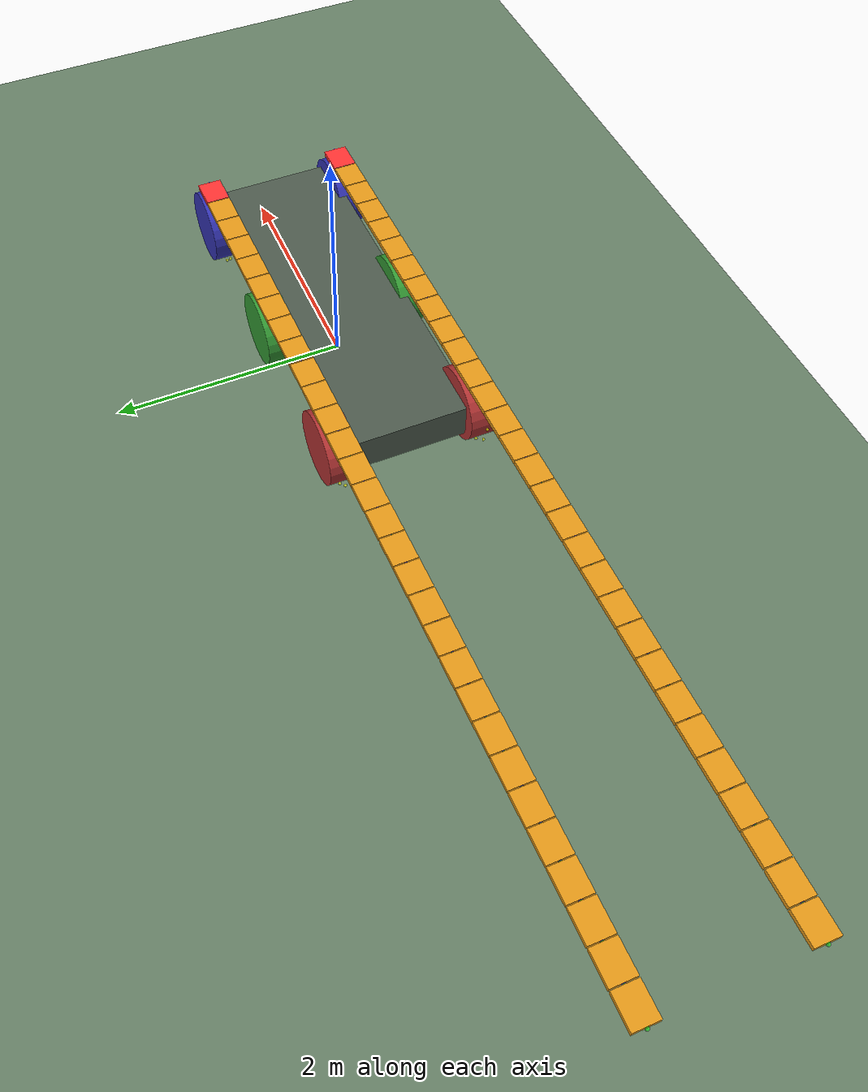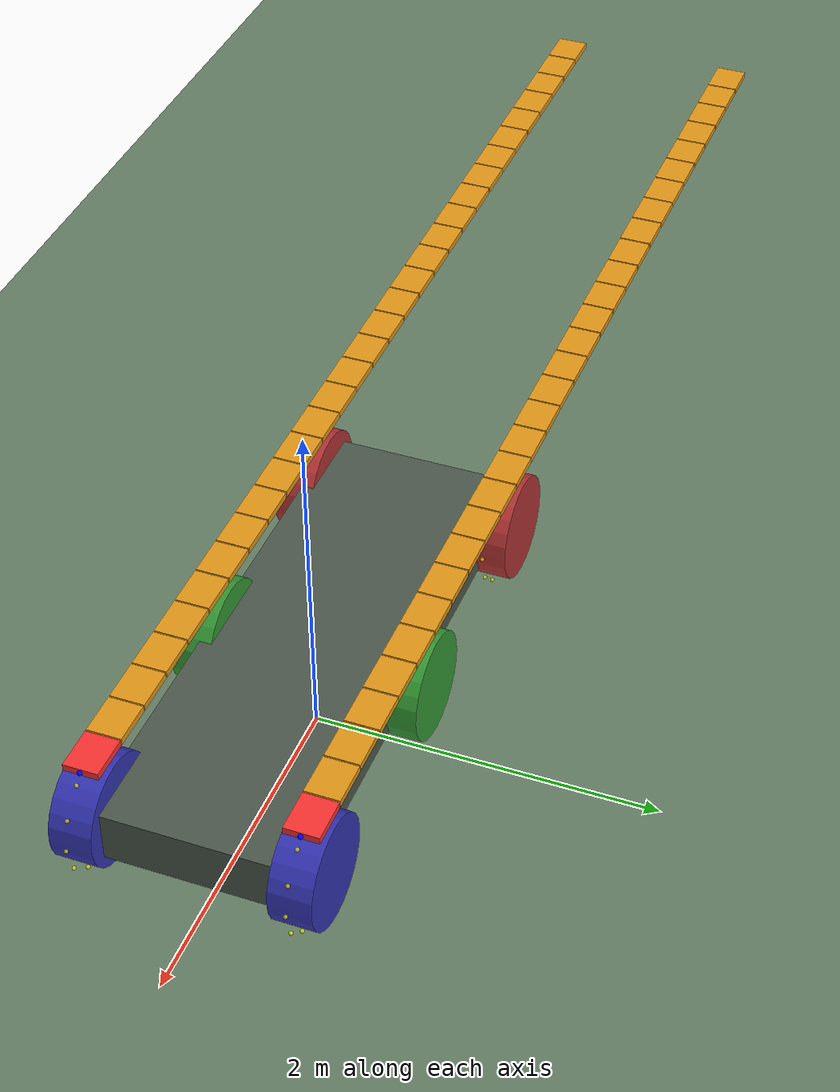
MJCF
<mujoco model="tank">
  <option timestep="0.002" gravity="0 0 -9.81" iterations="500" solver="Newton" tolerance="1e-12" noslip_iterations="20"/>
  <size nconmax="2000" njmax="6000"/>
  <default>
    <geom friction="0.8 0.01 0.01" condim="4" margin="0.01"/>
    <equality solref="0.005 1" solimp="0.95 0.99 0.001"/>
  </default>
  <worldbody>
    <camera name="overview" pos="0 -5 3" xyaxes="1 0 0 0 0.5 1" fovy="50"/>
    <camera name="top" pos="0 0 6" xyaxes="1 0 0 0 1 0" fovy="60"/>
    <light pos="0 -3 5" dir="0 0.5 -1" diffuse="1 1 1"/>
    <light pos="2 2 5" dir="-0.3 -0.3 -1" diffuse="0.5 0.5 0.5"/>
    <geom name="ground" type="plane" size="10 10 0.1" rgba="0.4 0.5 0.4 1"     contype="1" conaffinity="3" pos="0 0 0"/>
    <body name="hull" pos="0 0 0.5">
      <freejoint name="hull_jnt"/>
      <geom name="hull_body" type="box" size="1.5999999999999999 0.5499999999999999 0.15" rgba="0.3 0.35 0.3 1" mass="20.0" contype="0" conaffinity="0"/>
      <body name="left_drive_sprocket" pos="-1.4 0.6 0">
        <joint name="left_drive_hinge" type="hinge" axis="0 1 0" damping="0.2"/>
        <geom type="cylinder" size="0.31 0.12" euler="90 0 0" rgba="0.7 0.2 0.2 1" contype="0" conaffinity="0"/>
        <geom type="sphere" size="0.012" pos="0.3500 0 0.0000" rgba="1 1 0 0.6" contype="0" conaffinity="0"/>
        <geom type="sphere" size="0.012" pos="0.3031 0 0.1750" rgba="1 1 0 0.6" contype="0" conaffinity="0"/>
        <geom type="sphere" size="0.012" pos="0.1750 0 0.3031" rgba="1 1 0 0.6" contype="0" conaffinity="0"/>
        <geom type="sphere" size="0.012" pos="0.0000 0 0.3500" rgba="1 1 0 0.6" contype="0" conaffinity="0"/>
        <geom type="sphere" size="0.012" pos="-0.1750 0 0.3031" rgba="1 1 0 0.6" contype="0" conaffinity="0"/>
        <geom type="sphere" size="0.012" pos="-0.3031 0 0.1750" rgba="1 1 0 0.6" contype="0" conaffinity="0"/>
        <geom type="sphere" size="0.012" pos="-0.3500 0 0.0000" rgba="1 1 0 0.6" contype="0" conaffinity="0"/>
        <geom type="sphere" size="0.012" pos="-0.3031 0 -0.1750" rgba="1 1 0 0.6" contype="0" conaffinity="0"/>
        <geom type="sphere" size="0.012" pos="-0.1750 0 -0.3031" rgba="1 1 0 0.6" contype="0" conaffinity="0"/>
        <geom type="sphere" size="0.012" pos="-0.0000 0 -0.3500" rgba="1 1 0 0.6" contype="0" conaffinity="0"/>
        <geom type="sphere" size="0.012" pos="0.1750 0 -0.3031" rgba="1 1 0 0.6" contype="0" conaffinity="0"/>
        <geom type="sphere" size="0.012" pos="0.3031 0 -0.1750" rgba="1 1 0 0.6" contype="0" conaffinity="0"/>
      </body>
      <body name="left_idler_sprocket" pos="1.4 0.6 0">
        <joint name="left_idler_slide" type="slide" axis="1 0 0" stiffness="80.0" damping="80" range="-0.05 0.3"/>
        <joint name="left_idler_hinge" type="hinge" axis="0 1 0" damping="0.2"/>
        <geom type="cylinder" size="0.31 0.12" euler="90 0 0" rgba="0.2 0.2 0.7 1" contype="0" conaffinity="0"/>
        <geom type="sphere" size="0.012" pos="0.3500 0 0.0000" rgba="1 1 0 0.6" contype="0" conaffinity="0"/>
        <geom type="sphere" size="0.012" pos="0.3031 0 0.1750" rgba="1 1 0 0.6" contype="0" conaffinity="0"/>
        <geom type="sphere" size="0.012" pos="0.1750 0 0.3031" rgba="1 1 0 0.6" contype="0" conaffinity="0"/>
        <geom type="sphere" size="0.012" pos="0.0000 0 0.3500" rgba="1 1 0 0.6" contype="0" conaffinity="0"/>
        <geom type="sphere" size="0.012" pos="-0.1750 0 0.3031" rgba="1 1 0 0.6" contype="0" conaffinity="0"/>
        <geom type="sphere" size="0.012" pos="-0.3031 0 0.1750" rgba="1 1 0 0.6" contype="0" conaffinity="0"/>
        <geom type="sphere" size="0.012" pos="-0.3500 0 0.0000" rgba="1 1 0 0.6" contype="0" conaffinity="0"/>
        <geom type="sphere" size="0.012" pos="-0.3031 0 -0.1750" rgba="1 1 0 0.6" contype="0" conaffinity="0"/>
        <geom type="sphere" size="0.012" pos="-0.1750 0 -0.3031" rgba="1 1 0 0.6" contype="0" conaffinity="0"/>
        <geom type="sphere" size="0.012" pos="-0.0000 0 -0.3500" rgba="1 1 0 0.6" contype="0" conaffinity="0"/>
        <geom type="sphere" size="0.012" pos="0.1750 0 -0.3031" rgba="1 1 0 0.6" contype="0" conaffinity="0"/>
        <geom type="sphere" size="0.012" pos="0.3031 0 -0.1750" rgba="1 1 0 0.6" contype="0" conaffinity="0"/>
      </body>
      <body name="left_mid_sprocket" pos="0.0 0.6 0">
        <joint name="left_mid_hinge" type="hinge" axis="0 1 0" damping="0.2"/>
        <geom type="cylinder" size="0.31 0.12" euler="90 0 0" rgba="0.2 0.6 0.2 1" contype="0" conaffinity="0"/>
      </body>
      <body name="right_drive_sprocket" pos="-1.4 -0.6 0">
        <joint name="right_drive_hinge" type="hinge" axis="0 1 0" damping="0.2"/>
        <geom type="cylinder" size="0.31 0.12" euler="90 0 0" rgba="0.7 0.2 0.2 1" contype="0" conaffinity="0"/>
        <geom type="sphere" size="0.012" pos="0.3500 0 0.0000" rgba="1 1 0 0.6" contype="0" conaffinity="0"/>
        <geom type="sphere" size="0.012" pos="0.3031 0 0.1750" rgba="1 1 0 0.6" contype="0" conaffinity="0"/>
        <geom type="sphere" size="0.012" pos="0.1750 0 0.3031" rgba="1 1 0 0.6" contype="0" conaffinity="0"/>
        <geom type="sphere" size="0.012" pos="0.0000 0 0.3500" rgba="1 1 0 0.6" contype="0" conaffinity="0"/>
        <geom type="sphere" size="0.012" pos="-0.1750 0 0.3031" rgba="1 1 0 0.6" contype="0" conaffinity="0"/>
        <geom type="sphere" size="0.012" pos="-0.3031 0 0.1750" rgba="1 1 0 0.6" contype="0" conaffinity="0"/>
        <geom type="sphere" size="0.012" pos="-0.3500 0 0.0000" rgba="1 1 0 0.6" contype="0" conaffinity="0"/>
        <geom type="sphere" size="0.012" pos="-0.3031 0 -0.1750" rgba="1 1 0 0.6" contype="0" conaffinity="0"/>
        <geom type="sphere" size="0.012" pos="-0.1750 0 -0.3031" rgba="1 1 0 0.6" contype="0" conaffinity="0"/>
        <geom type="sphere" size="0.012" pos="-0.0000 0 -0.3500" rgba="1 1 0 0.6" contype="0" conaffinity="0"/>
        <geom type="sphere" size="0.012" pos="0.1750 0 -0.3031" rgba="1 1 0 0.6" contype="0" conaffinity="0"/>
        <geom type="sphere" size="0.012" pos="0.3031 0 -0.1750" rgba="1 1 0 0.6" contype="0" conaffinity="0"/>
      </body>
      <body name="right_idler_sprocket" pos="1.4 -0.6 0">
        <joint name="right_idler_slide" type="slide" axis="1 0 0" stiffness="80.0" damping="80" range="-0.05 0.3"/>
        <joint name="right_idler_hinge" type="hinge" axis="0 1 0" damping="0.2"/>
        <geom type="cylinder" size="0.31 0.12" euler="90 0 0" rgba="0.2 0.2 0.7 1" contype="0" conaffinity="0"/>
        <geom type="sphere" size="0.012" pos="0.3500 0 0.0000" rgba="1 1 0 0.6" contype="0" conaffinity="0"/>
        <geom type="sphere" size="0.012" pos="0.3031 0 0.1750" rgba="1 1 0 0.6" contype="0" conaffinity="0"/>
        <geom type="sphere" size="0.012" pos="0.1750 0 0.3031" rgba="1 1 0 0.6" contype="0" conaffinity="0"/>
        <geom type="sphere" size="0.012" pos="0.0000 0 0.3500" rgba="1 1 0 0.6" contype="0" conaffinity="0"/>
        <geom type="sphere" size="0.012" pos="-0.1750 0 0.3031" rgba="1 1 0 0.6" contype="0" conaffinity="0"/>
        <geom type="sphere" size="0.012" pos="-0.3031 0 0.1750" rgba="1 1 0 0.6" contype="0" conaffinity="0"/>
        <geom type="sphere" size="0.012" pos="-0.3500 0 0.0000" rgba="1 1 0 0.6" contype="0" conaffinity="0"/>
        <geom type="sphere" size="0.012" pos="-0.3031 0 -0.1750" rgba="1 1 0 0.6" contype="0" conaffinity="0"/>
        <geom type="sphere" size="0.012" pos="-0.1750 0 -0.3031" rgba="1 1 0 0.6" contype="0" conaffinity="0"/>
        <geom type="sphere" size="0.012" pos="-0.0000 0 -0.3500" rgba="1 1 0 0.6" contype="0" conaffinity="0"/>
        <geom type="sphere" size="0.012" pos="0.1750 0 -0.3031" rgba="1 1 0 0.6" contype="0" conaffinity="0"/>
        <geom type="sphere" size="0.012" pos="0.3031 0 -0.1750" rgba="1 1 0 0.6" contype="0" conaffinity="0"/>
      </body>
      <body name="right_mid_sprocket" pos="0.0 -0.6 0">
        <joint name="right_mid_hinge" type="hinge" axis="0 1 0" damping="0.2"/>
        <geom type="cylinder" size="0.31 0.12" euler="90 0 0" rgba="0.2 0.6 0.2 1" contype="0" conaffinity="0"/>
      </body>
    </body>
    <body name="left_link_0" pos="1.400000 0.600000 0.850000" quat="0.000000 0 1.000000 0">
      <freejoint name="left_link_0_jnt"/>
      <geom type="box" size="0.1250 0.1 0.02" rgba="1.0 0.2 0.2 1" mass="0.05" contype="2" conaffinity="1"/>
      <geom type="sphere" size="0.015" pos="0.1300 0 0" rgba="0 1 0 1" contype="0" conaffinity="0"/>
      <geom type="sphere" size="0.015" pos="-0.1300 0 0" rgba="0 0 1 1" contype="0" conaffinity="0"/>
      <geom type="sphere" size="0.02" pos="0 0 0" rgba="1 0 1 1" contype="0" conaffinity="0"/>
      <body name="left_link_1" pos="0.259970 0 0">
        <joint name="left_hinge_1" type="hinge" axis="0 1 0" pos="-0.129985 0 0" damping="0.05"/>
        <geom type="box" size="0.1250 0.1 0.02" rgba="0.9 0.6 0.1 1" mass="0.05" contype="2" conaffinity="1"/>
        <geom type="sphere" size="0.015" pos="0.1300 0 0" rgba="0 1 0 0.5" contype="0" conaffinity="0"/>
        <geom type="sphere" size="0.015" pos="-0.1300 0 0" rgba="0 0 1 0.5" contype="0" conaffinity="0"/>
        <geom type="sphere" size="0.02" pos="0 0 0" rgba="1 0 1 0.5" contype="0" conaffinity="0"/>
      <body name="left_link_2" pos="0.259970 0 0">
        <joint name="left_hinge_2" type="hinge" axis="0 1 0" pos="-0.129985 0 0" damping="0.05"/>
        <geom type="box" size="0.1250 0.1 0.02" rgba="0.9 0.6 0.1 1" mass="0.05" contype="2" conaffinity="1"/>
        <geom type="sphere" size="0.015" pos="0.1300 0 0" rgba="0 1 0 0.5" contype="0" conaffinity="0"/>
        <geom type="sphere" size="0.015" pos="-0.1300 0 0" rgba="0 0 1 0.5" contype="0" conaffinity="0"/>
        <geom type="sphere" size="0.02" pos="0 0 0" rgba="1 0 1 0.5" contype="0" conaffinity="0"/>
      <body name="left_link_3" pos="0.259970 0 0">
        <joint name="left_hinge_3" type="hinge" axis="0 1 0" pos="-0.129985 0 0" damping="0.05"/>
        <geom type="box" size="0.1250 0.1 0.02" rgba="0.9 0.6 0.1 1" mass="0.05" contype="2" conaffinity="1"/>
        <geom type="sphere" size="0.015" pos="0.1300 0 0" rgba="0 1 0 0.5" contype="0" conaffinity="0"/>
        <geom type="sphere" size="0.015" pos="-0.1300 0 0" rgba="0 0 1 0.5" contype="0" conaffinity="0"/>
        <geom type="sphere" size="0.02" pos="0 0 0" rgba="1 0 1 0.5" contype="0" conaffinity="0"/>
      <body name="left_link_4" pos="0.259970 0 0">
        <joint name="left_hinge_4" type="hinge" axis="0 1 0" pos="-0.129985 0 0" damping="0.05"/>
        <geom type="box" size="0.1250 0.1 0.02" rgba="0.9 0.6 0.1 1" mass="0.05" contype="2" conaffinity="1"/>
        <geom type="sphere" size="0.015" pos="0.1300 0 0" rgba="0 1 0 0.5" contype="0" conaffinity="0"/>
        <geom type="sphere" size="0.015" pos="-0.1300 0 0" rgba="0 0 1 0.5" contype="0" conaffinity="0"/>
        <geom type="sphere" size="0.02" pos="0 0 0" rgba="1 0 1 0.5" contype="0" conaffinity="0"/>
      <body name="left_link_5" pos="0.259970 0 0">
        <joint name="left_hinge_5" type="hinge" axis="0 1 0" pos="-0.129985 0 0" damping="0.05"/>
        <geom type="box" size="0.1250 0.1 0.02" rgba="0.9 0.6 0.1 1" mass="0.05" contype="2" conaffinity="1"/>
        <geom type="sphere" size="0.015" pos="0.1300 0 0" rgba="0 1 0 0.5" contype="0" conaffinity="0"/>
        <geom type="sphere" size="0.015" pos="-0.1300 0 0" rgba="0 0 1 0.5" contype="0" conaffinity="0"/>
        <geom type="sphere" size="0.02" pos="0 0 0" rgba="1 0 1 0.5" contype="0" conaffinity="0"/>
      <body name="left_link_6" pos="0.259970 0 0">
        <joint name="left_hinge_6" type="hinge" axis="0 1 0" pos="-0.129985 0 0" damping="0.05"/>
        <geom type="box" size="0.1250 0.1 0.02" rgba="0.9 0.6 0.1 1" mass="0.05" contype="2" conaffinity="1"/>
        <geom type="sphere" size="0.015" pos="0.1300 0 0" rgba="0 1 0 0.5" contype="0" conaffinity="0"/>
        <geom type="sphere" size="0.015" pos="-0.1300 0 0" rgba="0 0 1 0.5" contype="0" conaffinity="0"/>
        <geom type="sphere" size="0.02" pos="0 0 0" rgba="1 0 1 0.5" contype="0" conaffinity="0"/>
      <body name="left_link_7" pos="0.259970 0 0">
        <joint name="left_hinge_7" type="hinge" axis="0 1 0" pos="-0.129985 0 0" damping="0.05"/>
        <geom type="box" size="0.1250 0.1 0.02" rgba="0.9 0.6 0.1 1" mass="0.05" contype="2" conaffinity="1"/>
        <geom type="sphere" size="0.015" pos="0.1300 0 0" rgba="0 1 0 0.5" contype="0" conaffinity="0"/>
        <geom type="sphere" size="0.015" pos="-0.1300 0 0" rgba="0 0 1 0.5" contype="0" conaffinity="0"/>
        <geom type="sphere" size="0.02" pos="0 0 0" rgba="1 0 1 0.5" contype="0" conaffinity="0"/>
      <body name="left_link_8" pos="0.259970 0 0">
        <joint name="left_hinge_8" type="hinge" axis="0 1 0" pos="-0.129985 0 0" damping="0.05"/>
        <geom type="box" size="0.1250 0.1 0.02" rgba="0.9 0.6 0.1 1" mass="0.05" contype="2" conaffinity="1"/>
        <geom type="sphere" size="0.015" pos="0.1300 0 0" rgba="0 1 0 0.5" contype="0" conaffinity="0"/>
        <geom type="sphere" size="0.015" pos="-0.1300 0 0" rgba="0 0 1 0.5" contype="0" conaffinity="0"/>
        <geom type="sphere" size="0.02" pos="0 0 0" rgba="1 0 1 0.5" contype="0" conaffinity="0"/>
      <body name="left_link_9" pos="0.259970 0 0">
        <joint name="left_hinge_9" type="hinge" axis="0 1 0" pos="-0.129985 0 0" damping="0.05"/>
        <geom type="box" size="0.1250 0.1 0.02" rgba="0.9 0.6 0.1 1" mass="0.05" contype="2" conaffinity="1"/>
        <geom type="sphere" size="0.015" pos="0.1300 0 0" rgba="0 1 0 0.5" contype="0" conaffinity="0"/>
        <geom type="sphere" size="0.015" pos="-0.1300 0 0" rgba="0 0 1 0.5" contype="0" conaffinity="0"/>
        <geom type="sphere" size="0.02" pos="0 0 0" rgba="1 0 1 0.5" contype="0" conaffinity="0"/>
      <body name="left_link_10" pos="0.259970 0 0">
        <joint name="left_hinge_10" type="hinge" axis="0 1 0" pos="-0.129985 0 0" damping="0.05"/>
        <geom type="box" size="0.1250 0.1 0.02" rgba="0.9 0.6 0.1 1" mass="0.05" contype="2" conaffinity="1"/>
        <geom type="sphere" size="0.015" pos="0.1300 0 0" rgba="0 1 0 0.5" contype="0" conaffinity="0"/>
        <geom type="sphere" size="0.015" pos="-0.1300 0 0" rgba="0 0 1 0.5" contype="0" conaffinity="0"/>
        <geom type="sphere" size="0.02" pos="0 0 0" rgba="1 0 1 0.5" contype="0" conaffinity="0"/>
      <body name="left_link_11" pos="0.259970 0 0">
        <joint name="left_hinge_11" type="hinge" axis="0 1 0" pos="-0.129985 0 0" damping="0.05"/>
        <geom type="box" size="0.1250 0.1 0.02" rgba="0.9 0.6 0.1 1" mass="0.05" contype="2" conaffinity="1"/>
        <geom type="sphere" size="0.015" pos="0.1300 0 0" rgba="0 1 0 0.5" contype="0" conaffinity="0"/>
        <geom type="sphere" size="0.015" pos="-0.1300 0 0" rgba="0 0 1 0.5" contype="0" conaffinity="0"/>
        <geom type="sphere" size="0.02" pos="0 0 0" rgba="1 0 1 0.5" contype="0" conaffinity="0"/>
      <body name="left_link_12" pos="0.259970 0 0">
        <joint name="left_hinge_12" type="hinge" axis="0 1 0" pos="-0.129985 0 0" damping="0.05"/>
        <geom type="box" size="0.1250 0.1 0.02" rgba="0.9 0.6 0.1 1" mass="0.05" contype="2" conaffinity="1"/>
        <geom type="sphere" size="0.015" pos="0.1300 0 0" rgba="0 1 0 0.5" contype="0" conaffinity="0"/>
        <geom type="sphere" size="0.015" pos="-0.1300 0 0" rgba="0 0 1 0.5" contype="0" conaffinity="0"/>
        <geom type="sphere" size="0.02" pos="0 0 0" rgba="1 0 1 0.5" contype="0" conaffinity="0"/>
      <body name="left_link_13" pos="0.259970 0 0">
        <joint name="left_hinge_13" type="hinge" axis="0 1 0" pos="-0.129985 0 0" damping="0.05"/>
        <geom type="box" size="0.1250 0.1 0.02" rgba="0.9 0.6 0.1 1" mass="0.05" contype="2" conaffinity="1"/>
        <geom type="sphere" size="0.015" pos="0.1300 0 0" rgba="0 1 0 0.5" contype="0" conaffinity="0"/>
        <geom type="sphere" size="0.015" pos="-0.1300 0 0" rgba="0 0 1 0.5" contype="0" conaffinity="0"/>
        <geom type="sphere" size="0.02" pos="0 0 0" rgba="1 0 1 0.5" contype="0" conaffinity="0"/>
      <body name="left_link_14" pos="0.259970 0 0">
        <joint name="left_hinge_14" type="hinge" axis="0 1 0" pos="-0.129985 0 0" damping="0.05"/>
        <geom type="box" size="0.1250 0.1 0.02" rgba="0.9 0.6 0.1 1" mass="0.05" contype="2" conaffinity="1"/>
        <geom type="sphere" size="0.015" pos="0.1300 0 0" rgba="0 1 0 0.5" contype="0" conaffinity="0"/>
        <geom type="sphere" size="0.015" pos="-0.1300 0 0" rgba="0 0 1 0.5" contype="0" conaffinity="0"/>
        <geom type="sphere" size="0.02" pos="0 0 0" rgba="1 0 1 0.5" contype="0" conaffinity="0"/>
      <body name="left_link_15" pos="0.259970 0 0">
        <joint name="left_hinge_15" type="hinge" axis="0 1 0" pos="-0.129985 0 0" damping="0.05"/>
        <geom type="box" size="0.1250 0.1 0.02" rgba="0.9 0.6 0.1 1" mass="0.05" contype="2" conaffinity="1"/>
        <geom type="sphere" size="0.015" pos="0.1300 0 0" rgba="0 1 0 0.5" contype="0" conaffinity="0"/>
        <geom type="sphere" size="0.015" pos="-0.1300 0 0" rgba="0 0 1 0.5" contype="0" conaffinity="0"/>
        <geom type="sphere" size="0.02" pos="0 0 0" rgba="1 0 1 0.5" contype="0" conaffinity="0"/>
      <body name="left_link_16" pos="0.259970 0 0">
        <joint name="left_hinge_16" type="hinge" axis="0 1 0" pos="-0.129985 0 0" damping="0.05"/>
        <geom type="box" size="0.1250 0.1 0.02" rgba="0.9 0.6 0.1 1" mass="0.05" contype="2" conaffinity="1"/>
        <geom type="sphere" size="0.015" pos="0.1300 0 0" rgba="0 1 0 0.5" contype="0" conaffinity="0"/>
        <geom type="sphere" size="0.015" pos="-0.1300 0 0" rgba="0 0 1 0.5" contype="0" conaffinity="0"/>
        <geom type="sphere" size="0.02" pos="0 0 0" rgba="1 0 1 0.5" contype="0" conaffinity="0"/>
      <body name="left_link_17" pos="0.259970 0 0">
        <joint name="left_hinge_17" type="hinge" axis="0 1 0" pos="-0.129985 0 0" damping="0.05"/>
        <geom type="box" size="0.1250 0.1 0.02" rgba="0.9 0.6 0.1 1" mass="0.05" contype="2" conaffinity="1"/>
        <geom type="sphere" size="0.015" pos="0.1300 0 0" rgba="0 1 0 0.5" contype="0" conaffinity="0"/>
        <geom type="sphere" size="0.015" pos="-0.1300 0 0" rgba="0 0 1 0.5" contype="0" conaffinity="0"/>
        <geom type="sphere" size="0.02" pos="0 0 0" rgba="1 0 1 0.5" contype="0" conaffinity="0"/>
      <body name="left_link_18" pos="0.259970 0 0">
        <joint name="left_hinge_18" type="hinge" axis="0 1 0" pos="-0.129985 0 0" damping="0.05"/>
        <geom type="box" size="0.1250 0.1 0.02" rgba="0.9 0.6 0.1 1" mass="0.05" contype="2" conaffinity="1"/>
        <geom type="sphere" size="0.015" pos="0.1300 0 0" rgba="0 1 0 0.5" contype="0" conaffinity="0"/>
        <geom type="sphere" size="0.015" pos="-0.1300 0 0" rgba="0 0 1 0.5" contype="0" conaffinity="0"/>
        <geom type="sphere" size="0.02" pos="0 0 0" rgba="1 0 1 0.5" contype="0" conaffinity="0"/>
      <body name="left_link_19" pos="0.259970 0 0">
        <joint name="left_hinge_19" type="hinge" axis="0 1 0" pos="-0.129985 0 0" damping="0.05"/>
        <geom type="box" size="0.1250 0.1 0.02" rgba="0.9 0.6 0.1 1" mass="0.05" contype="2" conaffinity="1"/>
        <geom type="sphere" size="0.015" pos="0.1300 0 0" rgba="0 1 0 0.5" contype="0" conaffinity="0"/>
        <geom type="sphere" size="0.015" pos="-0.1300 0 0" rgba="0 0 1 0.5" contype="0" conaffinity="0"/>
        <geom type="sphere" size="0.02" pos="0 0 0" rgba="1 0 1 0.5" contype="0" conaffinity="0"/>
      <body name="left_link_20" pos="0.259970 0 0">
        <joint name="left_hinge_20" type="hinge" axis="0 1 0" pos="-0.129985 0 0" damping="0.05"/>
        <geom type="box" size="0.1250 0.1 0.02" rgba="0.9 0.6 0.1 1" mass="0.05" contype="2" conaffinity="1"/>
        <geom type="sphere" size="0.015" pos="0.1300 0 0" rgba="0 1 0 0.5" contype="0" conaffinity="0"/>
        <geom type="sphere" size="0.015" pos="-0.1300 0 0" rgba="0 0 1 0.5" contype="0" conaffinity="0"/>
        <geom type="sphere" size="0.02" pos="0 0 0" rgba="1 0 1 0.5" contype="0" conaffinity="0"/>
      <body name="left_link_21" pos="0.259970 0 0">
        <joint name="left_hinge_21" type="hinge" axis="0 1 0" pos="-0.129985 0 0" damping="0.05"/>
        <geom type="box" size="0.1250 0.1 0.02" rgba="0.9 0.6 0.1 1" mass="0.05" contype="2" conaffinity="1"/>
        <geom type="sphere" size="0.015" pos="0.1300 0 0" rgba="0 1 0 0.5" contype="0" conaffinity="0"/>
        <geom type="sphere" size="0.015" pos="-0.1300 0 0" rgba="0 0 1 0.5" contype="0" conaffinity="0"/>
        <geom type="sphere" size="0.02" pos="0 0 0" rgba="1 0 1 0.5" contype="0" conaffinity="0"/>
      <body name="left_link_22" pos="0.259970 0 0">
        <joint name="left_hinge_22" type="hinge" axis="0 1 0" pos="-0.129985 0 0" damping="0.05"/>
        <geom type="box" size="0.1250 0.1 0.02" rgba="0.9 0.6 0.1 1" mass="0.05" contype="2" conaffinity="1"/>
        <geom type="sphere" size="0.015" pos="0.1300 0 0" rgba="0 1 0 0.5" contype="0" conaffinity="0"/>
        <geom type="sphere" size="0.015" pos="-0.1300 0 0" rgba="0 0 1 0.5" contype="0" conaffinity="0"/>
        <geom type="sphere" size="0.02" pos="0 0 0" rgba="1 0 1 0.5" contype="0" conaffinity="0"/>
      <body name="left_link_23" pos="0.259970 0 0">
        <joint name="left_hinge_23" type="hinge" axis="0 1 0" pos="-0.129985 0 0" damping="0.05"/>
        <geom type="box" size="0.1250 0.1 0.02" rgba="0.9 0.6 0.1 1" mass="0.05" contype="2" conaffinity="1"/>
        <geom type="sphere" size="0.015" pos="0.1300 0 0" rgba="0 1 0 0.5" contype="0" conaffinity="0"/>
        <geom type="sphere" size="0.015" pos="-0.1300 0 0" rgba="0 0 1 0.5" contype="0" conaffinity="0"/>
        <geom type="sphere" size="0.02" pos="0 0 0" rgba="1 0 1 0.5" contype="0" conaffinity="0"/>
      <body name="left_link_24" pos="0.259970 0 0">
        <joint name="left_hinge_24" type="hinge" axis="0 1 0" pos="-0.129985 0 0" damping="0.05"/>
        <geom type="box" size="0.1250 0.1 0.02" rgba="0.9 0.6 0.1 1" mass="0.05" contype="2" conaffinity="1"/>
        <geom type="sphere" size="0.015" pos="0.1300 0 0" rgba="0 1 0 0.5" contype="0" conaffinity="0"/>
        <geom type="sphere" size="0.015" pos="-0.1300 0 0" rgba="0 0 1 0.5" contype="0" conaffinity="0"/>
        <geom type="sphere" size="0.02" pos="0 0 0" rgba="1 0 1 0.5" contype="0" conaffinity="0"/>
      <body name="left_link_25" pos="0.259970 0 0">
        <joint name="left_hinge_25" type="hinge" axis="0 1 0" pos="-0.129985 0 0" damping="0.05"/>
        <geom type="box" size="0.1250 0.1 0.02" rgba="0.9 0.6 0.1 1" mass="0.05" contype="2" conaffinity="1"/>
        <geom type="sphere" size="0.015" pos="0.1300 0 0" rgba="0 1 0 0.5" contype="0" conaffinity="0"/>
        <geom type="sphere" size="0.015" pos="-0.1300 0 0" rgba="0 0 1 0.5" contype="0" conaffinity="0"/>
        <geom type="sphere" size="0.02" pos="0 0 0" rgba="1 0 1 0.5" contype="0" conaffinity="0"/>
      <body name="left_link_26" pos="0.259970 0 0">
        <joint name="left_hinge_26" type="hinge" axis="0 1 0" pos="-0.129985 0 0" damping="0.05"/>
        <geom type="box" size="0.1250 0.1 0.02" rgba="0.9 0.6 0.1 1" mass="0.05" contype="2" conaffinity="1"/>
        <geom type="sphere" size="0.015" pos="0.1300 0 0" rgba="0 1 0 0.5" contype="0" conaffinity="0"/>
        <geom type="sphere" size="0.015" pos="-0.1300 0 0" rgba="0 0 1 0.5" contype="0" conaffinity="0"/>
        <geom type="sphere" size="0.02" pos="0 0 0" rgba="1 0 1 0.5" contype="0" conaffinity="0"/>
      <body name="left_link_27" pos="0.259970 0 0">
        <joint name="left_hinge_27" type="hinge" axis="0 1 0" pos="-0.129985 0 0" damping="0.05"/>
        <geom type="box" size="0.1250 0.1 0.02" rgba="0.9 0.6 0.1 1" mass="0.05" contype="2" conaffinity="1"/>
        <geom type="sphere" size="0.015" pos="0.1300 0 0" rgba="0 1 0 0.5" contype="0" conaffinity="0"/>
        <geom type="sphere" size="0.015" pos="-0.1300 0 0" rgba="0 0 1 0.5" contype="0" conaffinity="0"/>
        <geom type="sphere" size="0.02" pos="0 0 0" rgba="1 0 1 0.5" contype="0" conaffinity="0"/>
      <body name="left_link_28" pos="0.259970 0 0">
        <joint name="left_hinge_28" type="hinge" axis="0 1 0" pos="-0.129985 0 0" damping="0.05"/>
        <geom type="box" size="0.1250 0.1 0.02" rgba="0.9 0.6 0.1 1" mass="0.05" contype="2" conaffinity="1"/>
        <geom type="sphere" size="0.015" pos="0.1300 0 0" rgba="0 1 0 0.5" contype="0" conaffinity="0"/>
        <geom type="sphere" size="0.015" pos="-0.1300 0 0" rgba="0 0 1 0.5" contype="0" conaffinity="0"/>
        <geom type="sphere" size="0.02" pos="0 0 0" rgba="1 0 1 0.5" contype="0" conaffinity="0"/>
      <body name="left_link_29" pos="0.259970 0 0">
        <joint name="left_hinge_29" type="hinge" axis="0 1 0" pos="-0.129985 0 0" damping="0.05"/>
        <geom type="box" size="0.1250 0.1 0.02" rgba="0.9 0.6 0.1 1" mass="0.05" contype="2" conaffinity="1"/>
        <geom type="sphere" size="0.015" pos="0.1300 0 0" rgba="0 1 0 0.5" contype="0" conaffinity="0"/>
        <geom type="sphere" size="0.015" pos="-0.1300 0 0" rgba="0 0 1 0.5" contype="0" conaffinity="0"/>
        <geom type="sphere" size="0.02" pos="0 0 0" rgba="1 0 1 0.5" contype="0" conaffinity="0"/>
    </body>
    </body>
    </body>
    </body>
    </body>
    </body>
    </body>
    </body>
    </body>
    </body>
    </body>
    </body>
    </body>
    </body>
    </body>
    </body>
    </body>
    </body>
    </body>
    </body>
    </body>
    </body>
    </body>
    </body>
    </body>
    </body>
    </body>
    </body>
    </body>
    </body>
    <body name="right_link_0" pos="1.400000 -0.600000 0.850000" quat="0.000000 0 1.000000 0">
      <freejoint name="right_link_0_jnt"/>
      <geom type="box" size="0.1250 0.1 0.02" rgba="1.0 0.2 0.2 1" mass="0.05" contype="2" conaffinity="1"/>
      <geom type="sphere" size="0.015" pos="0.1300 0 0" rgba="0 1 0 1" contype="0" conaffinity="0"/>
      <geom type="sphere" size="0.015" pos="-0.1300 0 0" rgba="0 0 1 1" contype="0" conaffinity="0"/>
      <geom type="sphere" size="0.02" pos="0 0 0" rgba="1 0 1 1" contype="0" conaffinity="0"/>
      <body name="right_link_1" pos="0.259970 0 0">
        <joint name="right_hinge_1" type="hinge" axis="0 1 0" pos="-0.129985 0 0" damping="0.05"/>
        <geom type="box" size="0.1250 0.1 0.02" rgba="0.9 0.6 0.1 1" mass="0.05" contype="2" conaffinity="1"/>
        <geom type="sphere" size="0.015" pos="0.1300 0 0" rgba="0 1 0 0.5" contype="0" conaffinity="0"/>
        <geom type="sphere" size="0.015" pos="-0.1300 0 0" rgba="0 0 1 0.5" contype="0" conaffinity="0"/>
        <geom type="sphere" size="0.02" pos="0 0 0" rgba="1 0 1 0.5" contype="0" conaffinity="0"/>
      <body name="right_link_2" pos="0.259970 0 0">
        <joint name="right_hinge_2" type="hinge" axis="0 1 0" pos="-0.129985 0 0" damping="0.05"/>
        <geom type="box" size="0.1250 0.1 0.02" rgba="0.9 0.6 0.1 1" mass="0.05" contype="2" conaffinity="1"/>
        <geom type="sphere" size="0.015" pos="0.1300 0 0" rgba="0 1 0 0.5" contype="0" conaffinity="0"/>
        <geom type="sphere" size="0.015" pos="-0.1300 0 0" rgba="0 0 1 0.5" contype="0" conaffinity="0"/>
        <geom type="sphere" size="0.02" pos="0 0 0" rgba="1 0 1 0.5" contype="0" conaffinity="0"/>
      <body name="right_link_3" pos="0.259970 0 0">
        <joint name="right_hinge_3" type="hinge" axis="0 1 0" pos="-0.129985 0 0" damping="0.05"/>
        <geom type="box" size="0.1250 0.1 0.02" rgba="0.9 0.6 0.1 1" mass="0.05" contype="2" conaffinity="1"/>
        <geom type="sphere" size="0.015" pos="0.1300 0 0" rgba="0 1 0 0.5" contype="0" conaffinity="0"/>
        <geom type="sphere" size="0.015" pos="-0.1300 0 0" rgba="0 0 1 0.5" contype="0" conaffinity="0"/>
        <geom type="sphere" size="0.02" pos="0 0 0" rgba="1 0 1 0.5" contype="0" conaffinity="0"/>
      <body name="right_link_4" pos="0.259970 0 0">
        <joint name="right_hinge_4" type="hinge" axis="0 1 0" pos="-0.129985 0 0" damping="0.05"/>
        <geom type="box" size="0.1250 0.1 0.02" rgba="0.9 0.6 0.1 1" mass="0.05" contype="2" conaffinity="1"/>
        <geom type="sphere" size="0.015" pos="0.1300 0 0" rgba="0 1 0 0.5" contype="0" conaffinity="0"/>
        <geom type="sphere" size="0.015" pos="-0.1300 0 0" rgba="0 0 1 0.5" contype="0" conaffinity="0"/>
        <geom type="sphere" size="0.02" pos="0 0 0" rgba="1 0 1 0.5" contype="0" conaffinity="0"/>
      <body name="right_link_5" pos="0.259970 0 0">
        <joint name="right_hinge_5" type="hinge" axis="0 1 0" pos="-0.129985 0 0" damping="0.05"/>
        <geom type="box" size="0.1250 0.1 0.02" rgba="0.9 0.6 0.1 1" mass="0.05" contype="2" conaffinity="1"/>
        <geom type="sphere" size="0.015" pos="0.1300 0 0" rgba="0 1 0 0.5" contype="0" conaffinity="0"/>
        <geom type="sphere" size="0.015" pos="-0.1300 0 0" rgba="0 0 1 0.5" contype="0" conaffinity="0"/>
        <geom type="sphere" size="0.02" pos="0 0 0" rgba="1 0 1 0.5" contype="0" conaffinity="0"/>
      <body name="right_link_6" pos="0.259970 0 0">
        <joint name="right_hinge_6" type="hinge" axis="0 1 0" pos="-0.129985 0 0" damping="0.05"/>
        <geom type="box" size="0.1250 0.1 0.02" rgba="0.9 0.6 0.1 1" mass="0.05" contype="2" conaffinity="1"/>
        <geom type="sphere" size="0.015" pos="0.1300 0 0" rgba="0 1 0 0.5" contype="0" conaffinity="0"/>
        <geom type="sphere" size="0.015" pos="-0.1300 0 0" rgba="0 0 1 0.5" contype="0" conaffinity="0"/>
        <geom type="sphere" size="0.02" pos="0 0 0" rgba="1 0 1 0.5" contype="0" conaffinity="0"/>
      <body name="right_link_7" pos="0.259970 0 0">
        <joint name="right_hinge_7" type="hinge" axis="0 1 0" pos="-0.129985 0 0" damping="0.05"/>
        <geom type="box" size="0.1250 0.1 0.02" rgba="0.9 0.6 0.1 1" mass="0.05" contype="2" conaffinity="1"/>
        <geom type="sphere" size="0.015" pos="0.1300 0 0" rgba="0 1 0 0.5" contype="0" conaffinity="0"/>
        <geom type="sphere" size="0.015" pos="-0.1300 0 0" rgba="0 0 1 0.5" contype="0" conaffinity="0"/>
        <geom type="sphere" size="0.02" pos="0 0 0" rgba="1 0 1 0.5" contype="0" conaffinity="0"/>
      <body name="right_link_8" pos="0.259970 0 0">
        <joint name="right_hinge_8" type="hinge" axis="0 1 0" pos="-0.129985 0 0" damping="0.05"/>
        <geom type="box" size="0.1250 0.1 0.02" rgba="0.9 0.6 0.1 1" mass="0.05" contype="2" conaffinity="1"/>
        <geom type="sphere" size="0.015" pos="0.1300 0 0" rgba="0 1 0 0.5" contype="0" conaffinity="0"/>
        <geom type="sphere" size="0.015" pos="-0.1300 0 0" rgba="0 0 1 0.5" contype="0" conaffinity="0"/>
        <geom type="sphere" size="0.02" pos="0 0 0" rgba="1 0 1 0.5" contype="0" conaffinity="0"/>
      <body name="right_link_9" pos="0.259970 0 0">
        <joint name="right_hinge_9" type="hinge" axis="0 1 0" pos="-0.129985 0 0" damping="0.05"/>
        <geom type="box" size="0.1250 0.1 0.02" rgba="0.9 0.6 0.1 1" mass="0.05" contype="2" conaffinity="1"/>
        <geom type="sphere" size="0.015" pos="0.1300 0 0" rgba="0 1 0 0.5" contype="0" conaffinity="0"/>
        <geom type="sphere" size="0.015" pos="-0.1300 0 0" rgba="0 0 1 0.5" contype="0" conaffinity="0"/>
        <geom type="sphere" size="0.02" pos="0 0 0" rgba="1 0 1 0.5" contype="0" conaffinity="0"/>
      <body name="right_link_10" pos="0.259970 0 0">
        <joint name="right_hinge_10" type="hinge" axis="0 1 0" pos="-0.129985 0 0" damping="0.05"/>
        <geom type="box" size="0.1250 0.1 0.02" rgba="0.9 0.6 0.1 1" mass="0.05" contype="2" conaffinity="1"/>
        <geom type="sphere" size="0.015" pos="0.1300 0 0" rgba="0 1 0 0.5" contype="0" conaffinity="0"/>
        <geom type="sphere" size="0.015" pos="-0.1300 0 0" rgba="0 0 1 0.5" contype="0" conaffinity="0"/>
        <geom type="sphere" size="0.02" pos="0 0 0" rgba="1 0 1 0.5" contype="0" conaffinity="0"/>
      <body name="right_link_11" pos="0.259970 0 0">
        <joint name="right_hinge_11" type="hinge" axis="0 1 0" pos="-0.129985 0 0" damping="0.05"/>
        <geom type="box" size="0.1250 0.1 0.02" rgba="0.9 0.6 0.1 1" mass="0.05" contype="2" conaffinity="1"/>
        <geom type="sphere" size="0.015" pos="0.1300 0 0" rgba="0 1 0 0.5" contype="0" conaffinity="0"/>
        <geom type="sphere" size="0.015" pos="-0.1300 0 0" rgba="0 0 1 0.5" contype="0" conaffinity="0"/>
        <geom type="sphere" size="0.02" pos="0 0 0" rgba="1 0 1 0.5" contype="0" conaffinity="0"/>
      <body name="right_link_12" pos="0.259970 0 0">
        <joint name="right_hinge_12" type="hinge" axis="0 1 0" pos="-0.129985 0 0" damping="0.05"/>
        <geom type="box" size="0.1250 0.1 0.02" rgba="0.9 0.6 0.1 1" mass="0.05" contype="2" conaffinity="1"/>
        <geom type="sphere" size="0.015" pos="0.1300 0 0" rgba="0 1 0 0.5" contype="0" conaffinity="0"/>
        <geom type="sphere" size="0.015" pos="-0.1300 0 0" rgba="0 0 1 0.5" contype="0" conaffinity="0"/>
        <geom type="sphere" size="0.02" pos="0 0 0" rgba="1 0 1 0.5" contype="0" conaffinity="0"/>
      <body name="right_link_13" pos="0.259970 0 0">
        <joint name="right_hinge_13" type="hinge" axis="0 1 0" pos="-0.129985 0 0" damping="0.05"/>
        <geom type="box" size="0.1250 0.1 0.02" rgba="0.9 0.6 0.1 1" mass="0.05" contype="2" conaffinity="1"/>
        <geom type="sphere" size="0.015" pos="0.1300 0 0" rgba="0 1 0 0.5" contype="0" conaffinity="0"/>
        <geom type="sphere" size="0.015" pos="-0.1300 0 0" rgba="0 0 1 0.5" contype="0" conaffinity="0"/>
        <geom type="sphere" size="0.02" pos="0 0 0" rgba="1 0 1 0.5" contype="0" conaffinity="0"/>
      <body name="right_link_14" pos="0.259970 0 0">
        <joint name="right_hinge_14" type="hinge" axis="0 1 0" pos="-0.129985 0 0" damping="0.05"/>
        <geom type="box" size="0.1250 0.1 0.02" rgba="0.9 0.6 0.1 1" mass="0.05" contype="2" conaffinity="1"/>
        <geom type="sphere" size="0.015" pos="0.1300 0 0" rgba="0 1 0 0.5" contype="0" conaffinity="0"/>
        <geom type="sphere" size="0.015" pos="-0.1300 0 0" rgba="0 0 1 0.5" contype="0" conaffinity="0"/>
        <geom type="sphere" size="0.02" pos="0 0 0" rgba="1 0 1 0.5" contype="0" conaffinity="0"/>
      <body name="right_link_15" pos="0.259970 0 0">
        <joint name="right_hinge_15" type="hinge" axis="0 1 0" pos="-0.129985 0 0" damping="0.05"/>
        <geom type="box" size="0.1250 0.1 0.02" rgba="0.9 0.6 0.1 1" mass="0.05" contype="2" conaffinity="1"/>
        <geom type="sphere" size="0.015" pos="0.1300 0 0" rgba="0 1 0 0.5" contype="0" conaffinity="0"/>
        <geom type="sphere" size="0.015" pos="-0.1300 0 0" rgba="0 0 1 0.5" contype="0" conaffinity="0"/>
        <geom type="sphere" size="0.02" pos="0 0 0" rgba="1 0 1 0.5" contype="0" conaffinity="0"/>
      <body name="right_link_16" pos="0.259970 0 0">
        <joint name="right_hinge_16" type="hinge" axis="0 1 0" pos="-0.129985 0 0" damping="0.05"/>
        <geom type="box" size="0.1250 0.1 0.02" rgba="0.9 0.6 0.1 1" mass="0.05" contype="2" conaffinity="1"/>
        <geom type="sphere" size="0.015" pos="0.1300 0 0" rgba="0 1 0 0.5" contype="0" conaffinity="0"/>
        <geom type="sphere" size="0.015" pos="-0.1300 0 0" rgba="0 0 1 0.5" contype="0" conaffinity="0"/>
        <geom type="sphere" size="0.02" pos="0 0 0" rgba="1 0 1 0.5" contype="0" conaffinity="0"/>
      <body name="right_link_17" pos="0.259970 0 0">
        <joint name="right_hinge_17" type="hinge" axis="0 1 0" pos="-0.129985 0 0" damping="0.05"/>
        <geom type="box" size="0.1250 0.1 0.02" rgba="0.9 0.6 0.1 1" mass="0.05" contype="2" conaffinity="1"/>
        <geom type="sphere" size="0.015" pos="0.1300 0 0" rgba="0 1 0 0.5" contype="0" conaffinity="0"/>
        <geom type="sphere" size="0.015" pos="-0.1300 0 0" rgba="0 0 1 0.5" contype="0" conaffinity="0"/>
        <geom type="sphere" size="0.02" pos="0 0 0" rgba="1 0 1 0.5" contype="0" conaffinity="0"/>
      <body name="right_link_18" pos="0.259970 0 0">
        <joint name="right_hinge_18" type="hinge" axis="0 1 0" pos="-0.129985 0 0" damping="0.05"/>
        <geom type="box" size="0.1250 0.1 0.02" rgba="0.9 0.6 0.1 1" mass="0.05" contype="2" conaffinity="1"/>
        <geom type="sphere" size="0.015" pos="0.1300 0 0" rgba="0 1 0 0.5" contype="0" conaffinity="0"/>
        <geom type="sphere" size="0.015" pos="-0.1300 0 0" rgba="0 0 1 0.5" contype="0" conaffinity="0"/>
        <geom type="sphere" size="0.02" pos="0 0 0" rgba="1 0 1 0.5" contype="0" conaffinity="0"/>
      <body name="right_link_19" pos="0.259970 0 0">
        <joint name="right_hinge_19" type="hinge" axis="0 1 0" pos="-0.129985 0 0" damping="0.05"/>
        <geom type="box" size="0.1250 0.1 0.02" rgba="0.9 0.6 0.1 1" mass="0.05" contype="2" conaffinity="1"/>
        <geom type="sphere" size="0.015" pos="0.1300 0 0" rgba="0 1 0 0.5" contype="0" conaffinity="0"/>
        <geom type="sphere" size="0.015" pos="-0.1300 0 0" rgba="0 0 1 0.5" contype="0" conaffinity="0"/>
        <geom type="sphere" size="0.02" pos="0 0 0" rgba="1 0 1 0.5" contype="0" conaffinity="0"/>
      <body name="right_link_20" pos="0.259970 0 0">
        <joint name="right_hinge_20" type="hinge" axis="0 1 0" pos="-0.129985 0 0" damping="0.05"/>
        <geom type="box" size="0.1250 0.1 0.02" rgba="0.9 0.6 0.1 1" mass="0.05" contype="2" conaffinity="1"/>
        <geom type="sphere" size="0.015" pos="0.1300 0 0" rgba="0 1 0 0.5" contype="0" conaffinity="0"/>
        <geom type="sphere" size="0.015" pos="-0.1300 0 0" rgba="0 0 1 0.5" contype="0" conaffinity="0"/>
        <geom type="sphere" size="0.02" pos="0 0 0" rgba="1 0 1 0.5" contype="0" conaffinity="0"/>
      <body name="right_link_21" pos="0.259970 0 0">
        <joint name="right_hinge_21" type="hinge" axis="0 1 0" pos="-0.129985 0 0" damping="0.05"/>
        <geom type="box" size="0.1250 0.1 0.02" rgba="0.9 0.6 0.1 1" mass="0.05" contype="2" conaffinity="1"/>
        <geom type="sphere" size="0.015" pos="0.1300 0 0" rgba="0 1 0 0.5" contype="0" conaffinity="0"/>
        <geom type="sphere" size="0.015" pos="-0.1300 0 0" rgba="0 0 1 0.5" contype="0" conaffinity="0"/>
        <geom type="sphere" size="0.02" pos="0 0 0" rgba="1 0 1 0.5" contype="0" conaffinity="0"/>
      <body name="right_link_22" pos="0.259970 0 0">
        <joint name="right_hinge_22" type="hinge" axis="0 1 0" pos="-0.129985 0 0" damping="0.05"/>
        <geom type="box" size="0.1250 0.1 0.02" rgba="0.9 0.6 0.1 1" mass="0.05" contype="2" conaffinity="1"/>
        <geom type="sphere" size="0.015" pos="0.1300 0 0" rgba="0 1 0 0.5" contype="0" conaffinity="0"/>
        <geom type="sphere" size="0.015" pos="-0.1300 0 0" rgba="0 0 1 0.5" contype="0" conaffinity="0"/>
        <geom type="sphere" size="0.02" pos="0 0 0" rgba="1 0 1 0.5" contype="0" conaffinity="0"/>
      <body name="right_link_23" pos="0.259970 0 0">
        <joint name="right_hinge_23" type="hinge" axis="0 1 0" pos="-0.129985 0 0" damping="0.05"/>
        <geom type="box" size="0.1250 0.1 0.02" rgba="0.9 0.6 0.1 1" mass="0.05" contype="2" conaffinity="1"/>
        <geom type="sphere" size="0.015" pos="0.1300 0 0" rgba="0 1 0 0.5" contype="0" conaffinity="0"/>
        <geom type="sphere" size="0.015" pos="-0.1300 0 0" rgba="0 0 1 0.5" contype="0" conaffinity="0"/>
        <geom type="sphere" size="0.02" pos="0 0 0" rgba="1 0 1 0.5" contype="0" conaffinity="0"/>
      <body name="right_link_24" pos="0.259970 0 0">
        <joint name="right_hinge_24" type="hinge" axis="0 1 0" pos="-0.129985 0 0" damping="0.05"/>
        <geom type="box" size="0.1250 0.1 0.02" rgba="0.9 0.6 0.1 1" mass="0.05" contype="2" conaffinity="1"/>
        <geom type="sphere" size="0.015" pos="0.1300 0 0" rgba="0 1 0 0.5" contype="0" conaffinity="0"/>
        <geom type="sphere" size="0.015" pos="-0.1300 0 0" rgba="0 0 1 0.5" contype="0" conaffinity="0"/>
        <geom type="sphere" size="0.02" pos="0 0 0" rgba="1 0 1 0.5" contype="0" conaffinity="0"/>
      <body name="right_link_25" pos="0.259970 0 0">
        <joint name="right_hinge_25" type="hinge" axis="0 1 0" pos="-0.129985 0 0" damping="0.05"/>
        <geom type="box" size="0.1250 0.1 0.02" rgba="0.9 0.6 0.1 1" mass="0.05" contype="2" conaffinity="1"/>
        <geom type="sphere" size="0.015" pos="0.1300 0 0" rgba="0 1 0 0.5" contype="0" conaffinity="0"/>
        <geom type="sphere" size="0.015" pos="-0.1300 0 0" rgba="0 0 1 0.5" contype="0" conaffinity="0"/>
        <geom type="sphere" size="0.02" pos="0 0 0" rgba="1 0 1 0.5" contype="0" conaffinity="0"/>
      <body name="right_link_26" pos="0.259970 0 0">
        <joint name="right_hinge_26" type="hinge" axis="0 1 0" pos="-0.129985 0 0" damping="0.05"/>
        <geom type="box" size="0.1250 0.1 0.02" rgba="0.9 0.6 0.1 1" mass="0.05" contype="2" conaffinity="1"/>
        <geom type="sphere" size="0.015" pos="0.1300 0 0" rgba="0 1 0 0.5" contype="0" conaffinity="0"/>
        <geom type="sphere" size="0.015" pos="-0.1300 0 0" rgba="0 0 1 0.5" contype="0" conaffinity="0"/>
        <geom type="sphere" size="0.02" pos="0 0 0" rgba="1 0 1 0.5" contype="0" conaffinity="0"/>
      <body name="right_link_27" pos="0.259970 0 0">
        <joint name="right_hinge_27" type="hinge" axis="0 1 0" pos="-0.129985 0 0" damping="0.05"/>
        <geom type="box" size="0.1250 0.1 0.02" rgba="0.9 0.6 0.1 1" mass="0.05" contype="2" conaffinity="1"/>
        <geom type="sphere" size="0.015" pos="0.1300 0 0" rgba="0 1 0 0.5" contype="0" conaffinity="0"/>
        <geom type="sphere" size="0.015" pos="-0.1300 0 0" rgba="0 0 1 0.5" contype="0" conaffinity="0"/>
        <geom type="sphere" size="0.02" pos="0 0 0" rgba="1 0 1 0.5" contype="0" conaffinity="0"/>
      <body name="right_link_28" pos="0.259970 0 0">
        <joint name="right_hinge_28" type="hinge" axis="0 1 0" pos="-0.129985 0 0" damping="0.05"/>
        <geom type="box" size="0.1250 0.1 0.02" rgba="0.9 0.6 0.1 1" mass="0.05" contype="2" conaffinity="1"/>
        <geom type="sphere" size="0.015" pos="0.1300 0 0" rgba="0 1 0 0.5" contype="0" conaffinity="0"/>
        <geom type="sphere" size="0.015" pos="-0.1300 0 0" rgba="0 0 1 0.5" contype="0" conaffinity="0"/>
        <geom type="sphere" size="0.02" pos="0 0 0" rgba="1 0 1 0.5" contype="0" conaffinity="0"/>
      <body name="right_link_29" pos="0.259970 0 0">
        <joint name="right_hinge_29" type="hinge" axis="0 1 0" pos="-0.129985 0 0" damping="0.05"/>
        <geom type="box" size="0.1250 0.1 0.02" rgba="0.9 0.6 0.1 1" mass="0.05" contype="2" conaffinity="1"/>
        <geom type="sphere" size="0.015" pos="0.1300 0 0" rgba="0 1 0 0.5" contype="0" conaffinity="0"/>
        <geom type="sphere" size="0.015" pos="-0.1300 0 0" rgba="0 0 1 0.5" contype="0" conaffinity="0"/>
        <geom type="sphere" size="0.02" pos="0 0 0" rgba="1 0 1 0.5" contype="0" conaffinity="0"/>
    </body>
    </body>
    </body>
    </body>
    </body>
    </body>
    </body>
    </body>
    </body>
    </body>
    </body>
    </body>
    </body>
    </body>
    </body>
    </body>
    </body>
    </body>
    </body>
    </body>
    </body>
    </body>
    </body>
    </body>
    </body>
    </body>
    </body>
    </body>
    </body>
    </body>
  </worldbody>
  <actuator>
    <velocity name="left_drive_motor" joint="left_drive_hinge" kv="200" ctrllimited="true" ctrlrange="-5 5"/>
    <velocity name="left_idler_motor" joint="left_idler_hinge" kv="200" ctrllimited="true" ctrlrange="-5 5"/>
    <velocity name="left_mid_motor" joint="left_mid_hinge" kv="200" ctrllimited="true" ctrlrange="-5 5"/>
    <velocity name="right_drive_motor" joint="right_drive_hinge" kv="200" ctrllimited="true" ctrlrange="-5 5"/>
    <velocity name="right_idler_motor" joint="right_idler_hinge" kv="200" ctrllimited="true" ctrlrange="-5 5"/>
    <velocity name="right_mid_motor" joint="right_mid_hinge" kv="200" ctrllimited="true" ctrlrange="-5 5"/>
  </actuator>
  <equality>
    <connect name="left_loop_close" body1="left_link_29" body2="left_link_0" anchor="0.129985 0 0" active="true"/>
    <connect name="left_eng_0_drive_L" body1="left_drive_sprocket" body2="left_link_0" anchor="0 0 0" solref="0.005 1" solimp="0.95 0.99 0.001" active="false"/>
    <connect name="left_eng_0_drive_R" body1="left_drive_sprocket" body2="left_link_0" anchor="0 0 0" solref="0.005 1" solimp="0.95 0.99 0.001" active="false"/>
    <connect name="left_eng_0_idler_L" body1="left_idler_sprocket" body2="left_link_0" anchor="0 0 0" solref="0.005 1" solimp="0.95 0.99 0.001" active="false"/>
    <connect name="left_eng_0_idler_R" body1="left_idler_sprocket" body2="left_link_0" anchor="0 0 0" solref="0.005 1" solimp="0.95 0.99 0.001" active="false"/>
    <connect name="left_eng_0_mid_L" body1="left_mid_sprocket" body2="left_link_0" anchor="0 0 0" solref="0.005 1" solimp="0.95 0.99 0.001" active="false"/>
    <connect name="left_eng_0_mid_R" body1="left_mid_sprocket" body2="left_link_0" anchor="0 0 0" solref="0.005 1" solimp="0.95 0.99 0.001" active="false"/>
    <connect name="left_eng_1_drive_L" body1="left_drive_sprocket" body2="left_link_1" anchor="0 0 0" solref="0.005 1" solimp="0.95 0.99 0.001" active="false"/>
    <connect name="left_eng_1_drive_R" body1="left_drive_sprocket" body2="left_link_1" anchor="0 0 0" solref="0.005 1" solimp="0.95 0.99 0.001" active="false"/>
    <connect name="left_eng_1_idler_L" body1="left_idler_sprocket" body2="left_link_1" anchor="0 0 0" solref="0.005 1" solimp="0.95 0.99 0.001" active="false"/>
    <connect name="left_eng_1_idler_R" body1="left_idler_sprocket" body2="left_link_1" anchor="0 0 0" solref="0.005 1" solimp="0.95 0.99 0.001" active="false"/>
    <connect name="left_eng_1_mid_L" body1="left_mid_sprocket" body2="left_link_1" anchor="0 0 0" solref="0.005 1" solimp="0.95 0.99 0.001" active="false"/>
    <connect name="left_eng_1_mid_R" body1="left_mid_sprocket" body2="left_link_1" anchor="0 0 0" solref="0.005 1" solimp="0.95 0.99 0.001" active="false"/>
    <connect name="left_eng_2_drive_L" body1="left_drive_sprocket" body2="left_link_2" anchor="0 0 0" solref="0.005 1" solimp="0.95 0.99 0.001" active="false"/>
    <connect name="left_eng_2_drive_R" body1="left_drive_sprocket" body2="left_link_2" anchor="0 0 0" solref="0.005 1" solimp="0.95 0.99 0.001" active="false"/>
    <connect name="left_eng_2_idler_L" body1="left_idler_sprocket" body2="left_link_2" anchor="0 0 0" solref="0.005 1" solimp="0.95 0.99 0.001" active="false"/>
    <connect name="left_eng_2_idler_R" body1="left_idler_sprocket" body2="left_link_2" anchor="0 0 0" solref="0.005 1" solimp="0.95 0.99 0.001" active="false"/>
    <connect name="left_eng_2_mid_L" body1="left_mid_sprocket" body2="left_link_2" anchor="0 0 0" solref="0.005 1" solimp="0.95 0.99 0.001" active="false"/>
    <connect name="left_eng_2_mid_R" body1="left_mid_sprocket" body2="left_link_2" anchor="0 0 0" solref="0.005 1" solimp="0.95 0.99 0.001" active="false"/>
    <connect name="left_eng_3_drive_L" body1="left_drive_sprocket" body2="left_link_3" anchor="0 0 0" solref="0.005 1" solimp="0.95 0.99 0.001" active="false"/>
    <connect name="left_eng_3_drive_R" body1="left_drive_sprocket" body2="left_link_3" anchor="0 0 0" solref="0.005 1" solimp="0.95 0.99 0.001" active="false"/>
    <connect name="left_eng_3_idler_L" body1="left_idler_sprocket" body2="left_link_3" anchor="0 0 0" solref="0.005 1" solimp="0.95 0.99 0.001" active="false"/>
    <connect name="left_eng_3_idler_R" body1="left_idler_sprocket" body2="left_link_3" anchor="0 0 0" solref="0.005 1" solimp="0.95 0.99 0.001" active="false"/>
    <connect name="left_eng_3_mid_L" body1="left_mid_sprocket" body2="left_link_3" anchor="0 0 0" solref="0.005 1" solimp="0.95 0.99 0.001" active="false"/>
    <connect name="left_eng_3_mid_R" body1="left_mid_sprocket" body2="left_link_3" anchor="0 0 0" solref="0.005 1" solimp="0.95 0.99 0.001" active="false"/>
    <connect name="left_eng_4_drive_L" body1="left_drive_sprocket" body2="left_link_4" anchor="0 0 0" solref="0.005 1" solimp="0.95 0.99 0.001" active="false"/>
    <connect name="left_eng_4_drive_R" body1="left_drive_sprocket" body2="left_link_4" anchor="0 0 0" solref="0.005 1" solimp="0.95 0.99 0.001" active="false"/>
    <connect name="left_eng_4_idler_L" body1="left_idler_sprocket" body2="left_link_4" anchor="0 0 0" solref="0.005 1" solimp="0.95 0.99 0.001" active="false"/>
    <connect name="left_eng_4_idler_R" body1="left_idler_sprocket" body2="left_link_4" anchor="0 0 0" solref="0.005 1" solimp="0.95 0.99 0.001" active="false"/>
    <connect name="left_eng_4_mid_L" body1="left_mid_sprocket" body2="left_link_4" anchor="0 0 0" solref="0.005 1" solimp="0.95 0.99 0.001" active="false"/>
    <connect name="left_eng_4_mid_R" body1="left_mid_sprocket" body2="left_link_4" anchor="0 0 0" solref="0.005 1" solimp="0.95 0.99 0.001" active="false"/>
    <connect name="left_eng_5_drive_L" body1="left_drive_sprocket" body2="left_link_5" anchor="0 0 0" solref="0.005 1" solimp="0.95 0.99 0.001" active="false"/>
    <connect name="left_eng_5_drive_R" body1="left_drive_sprocket" body2="left_link_5" anchor="0 0 0" solref="0.005 1" solimp="0.95 0.99 0.001" active="false"/>
    <connect name="left_eng_5_idler_L" body1="left_idler_sprocket" body2="left_link_5" anchor="0 0 0" solref="0.005 1" solimp="0.95 0.99 0.001" active="false"/>
    <connect name="left_eng_5_idler_R" body1="left_idler_sprocket" body2="left_link_5" anchor="0 0 0" solref="0.005 1" solimp="0.95 0.99 0.001" active="false"/>
    <connect name="left_eng_5_mid_L" body1="left_mid_sprocket" body2="left_link_5" anchor="0 0 0" solref="0.005 1" solimp="0.95 0.99 0.001" active="false"/>
    <connect name="left_eng_5_mid_R" body1="left_mid_sprocket" body2="left_link_5" anchor="0 0 0" solref="0.005 1" solimp="0.95 0.99 0.001" active="false"/>
    <connect name="left_eng_6_drive_L" body1="left_drive_sprocket" body2="left_link_6" anchor="0 0 0" solref="0.005 1" solimp="0.95 0.99 0.001" active="false"/>
    <connect name="left_eng_6_drive_R" body1="left_drive_sprocket" body2="left_link_6" anchor="0 0 0" solref="0.005 1" solimp="0.95 0.99 0.001" active="false"/>
    <connect name="left_eng_6_idler_L" body1="left_idler_sprocket" body2="left_link_6" anchor="0 0 0" solref="0.005 1" solimp="0.95 0.99 0.001" active="false"/>
    <connect name="left_eng_6_idler_R" body1="left_idler_sprocket" body2="left_link_6" anchor="0 0 0" solref="0.005 1" solimp="0.95 0.99 0.001" active="false"/>
    <connect name="left_eng_6_mid_L" body1="left_mid_sprocket" body2="left_link_6" anchor="0 0 0" solref="0.005 1" solimp="0.95 0.99 0.001" active="false"/>
    <connect name="left_eng_6_mid_R" body1="left_mid_sprocket" body2="left_link_6" anchor="0 0 0" solref="0.005 1" solimp="0.95 0.99 0.001" active="false"/>
    <connect name="left_eng_7_drive_L" body1="left_drive_sprocket" body2="left_link_7" anchor="0 0 0" solref="0.005 1" solimp="0.95 0.99 0.001" active="false"/>
    <connect name="left_eng_7_drive_R" body1="left_drive_sprocket" body2="left_link_7" anchor="0 0 0" solref="0.005 1" solimp="0.95 0.99 0.001" active="false"/>
    <connect name="left_eng_7_idler_L" body1="left_idler_sprocket" body2="left_link_7" anchor="0 0 0" solref="0.005 1" solimp="0.95 0.99 0.001" active="false"/>
    <connect name="left_eng_7_idler_R" body1="left_idler_sprocket" body2="left_link_7" anchor="0 0 0" solref="0.005 1" solimp="0.95 0.99 0.001" active="false"/>
    <connect name="left_eng_7_mid_L" body1="left_mid_sprocket" body2="left_link_7" anchor="0 0 0" solref="0.005 1" solimp="0.95 0.99 0.001" active="false"/>
    <connect name="left_eng_7_mid_R" body1="left_mid_sprocket" body2="left_link_7" anchor="0 0 0" solref="0.005 1" solimp="0.95 0.99 0.001" active="false"/>
    <connect name="left_eng_8_drive_L" body1="left_drive_sprocket" body2="left_link_8" anchor="0 0 0" solref="0.005 1" solimp="0.95 0.99 0.001" active="false"/>
    <connect name="left_eng_8_drive_R" body1="left_drive_sprocket" body2="left_link_8" anchor="0 0 0" solref="0.005 1" solimp="0.95 0.99 0.001" active="false"/>
    <connect name="left_eng_8_idler_L" body1="left_idler_sprocket" body2="left_link_8" anchor="0 0 0" solref="0.005 1" solimp="0.95 0.99 0.001" active="false"/>
    <connect name="left_eng_8_idler_R" body1="left_idler_sprocket" body2="left_link_8" anchor="0 0 0" solref="0.005 1" solimp="0.95 0.99 0.001" active="false"/>
    <connect name="left_eng_8_mid_L" body1="left_mid_sprocket" body2="left_link_8" anchor="0 0 0" solref="0.005 1" solimp="0.95 0.99 0.001" active="false"/>
    <connect name="left_eng_8_mid_R" body1="left_mid_sprocket" body2="left_link_8" anchor="0 0 0" solref="0.005 1" solimp="0.95 0.99 0.001" active="false"/>
    <connect name="left_eng_9_drive_L" body1="left_drive_sprocket" body2="left_link_9" anchor="0 0 0" solref="0.005 1" solimp="0.95 0.99 0.001" active="false"/>
    <connect name="left_eng_9_drive_R" body1="left_drive_sprocket" body2="left_link_9" anchor="0 0 0" solref="0.005 1" solimp="0.95 0.99 0.001" active="false"/>
    <connect name="left_eng_9_idler_L" body1="left_idler_sprocket" body2="left_link_9" anchor="0 0 0" solref="0.005 1" solimp="0.95 0.99 0.001" active="false"/>
    <connect name="left_eng_9_idler_R" body1="left_idler_sprocket" body2="left_link_9" anchor="0 0 0" solref="0.005 1" solimp="0.95 0.99 0.001" active="false"/>
    <connect name="left_eng_9_mid_L" body1="left_mid_sprocket" body2="left_link_9" anchor="0 0 0" solref="0.005 1" solimp="0.95 0.99 0.001" active="false"/>
    <connect name="left_eng_9_mid_R" body1="left_mid_sprocket" body2="left_link_9" anchor="0 0 0" solref="0.005 1" solimp="0.95 0.99 0.001" active="false"/>
    <connect name="left_eng_10_drive_L" body1="left_drive_sprocket" body2="left_link_10" anchor="0 0 0" solref="0.005 1" solimp="0.95 0.99 0.001" active="false"/>
    <connect name="left_eng_10_drive_R" body1="left_drive_sprocket" body2="left_link_10" anchor="0 0 0" solref="0.005 1" solimp="0.95 0.99 0.001" active="false"/>
    <connect name="left_eng_10_idler_L" body1="left_idler_sprocket" body2="left_link_10" anchor="0 0 0" solref="0.005 1" solimp="0.95 0.99 0.001" active="false"/>
    <connect name="left_eng_10_idler_R" body1="left_idler_sprocket" body2="left_link_10" anchor="0 0 0" solref="0.005 1" solimp="0.95 0.99 0.001" active="false"/>
    <connect name="left_eng_10_mid_L" body1="left_mid_sprocket" body2="left_link_10" anchor="0 0 0" solref="0.005 1" solimp="0.95 0.99 0.001" active="false"/>
    <connect name="left_eng_10_mid_R" body1="left_mid_sprocket" body2="left_link_10" anchor="0 0 0" solref="0.005 1" solimp="0.95 0.99 0.001" active="false"/>
    <connect name="left_eng_11_drive_L" body1="left_drive_sprocket" body2="left_link_11" anchor="0 0 0" solref="0.005 1" solimp="0.95 0.99 0.001" active="false"/>
    <connect name="left_eng_11_drive_R" body1="left_drive_sprocket" body2="left_link_11" anchor="0 0 0" solref="0.005 1" solimp="0.95 0.99 0.001" active="false"/>
    <connect name="left_eng_11_idler_L" body1="left_idler_sprocket" body2="left_link_11" anchor="0 0 0" solref="0.005 1" solimp="0.95 0.99 0.001" active="false"/>
    <connect name="left_eng_11_idler_R" body1="left_idler_sprocket" body2="left_link_11" anchor="0 0 0" solref="0.005 1" solimp="0.95 0.99 0.001" active="false"/>
    <connect name="left_eng_11_mid_L" body1="left_mid_sprocket" body2="left_link_11" anchor="0 0 0" solref="0.005 1" solimp="0.95 0.99 0.001" active="false"/>
    <connect name="left_eng_11_mid_R" body1="left_mid_sprocket" body2="left_link_11" anchor="0 0 0" solref="0.005 1" solimp="0.95 0.99 0.001" active="false"/>
    <connect name="left_eng_12_drive_L" body1="left_drive_sprocket" body2="left_link_12" anchor="0 0 0" solref="0.005 1" solimp="0.95 0.99 0.001" active="false"/>
    <connect name="left_eng_12_drive_R" body1="left_drive_sprocket" body2="left_link_12" anchor="0 0 0" solref="0.005 1" solimp="0.95 0.99 0.001" active="false"/>
    <connect name="left_eng_12_idler_L" body1="left_idler_sprocket" body2="left_link_12" anchor="0 0 0" solref="0.005 1" solimp="0.95 0.99 0.001" active="false"/>
    <connect name="left_eng_12_idler_R" body1="left_idler_sprocket" body2="left_link_12" anchor="0 0 0" solref="0.005 1" solimp="0.95 0.99 0.001" active="false"/>
    <connect name="left_eng_12_mid_L" body1="left_mid_sprocket" body2="left_link_12" anchor="0 0 0" solref="0.005 1" solimp="0.95 0.99 0.001" active="false"/>
    <connect name="left_eng_12_mid_R" body1="left_mid_sprocket" body2="left_link_12" anchor="0 0 0" solref="0.005 1" solimp="0.95 0.99 0.001" active="false"/>
    <connect name="left_eng_13_drive_L" body1="left_drive_sprocket" body2="left_link_13" anchor="0 0 0" solref="0.005 1" solimp="0.95 0.99 0.001" active="false"/>
    <connect name="left_eng_13_drive_R" body1="left_drive_sprocket" body2="left_link_13" anchor="0 0 0" solref="0.005 1" solimp="0.95 0.99 0.001" active="false"/>
    <connect name="left_eng_13_idler_L" body1="left_idler_sprocket" body2="left_link_13" anchor="0 0 0" solref="0.005 1" solimp="0.95 0.99 0.001" active="false"/>
    <connect name="left_eng_13_idler_R" body1="left_idler_sprocket" body2="left_link_13" anchor="0 0 0" solref="0.005 1" solimp="0.95 0.99 0.001" active="false"/>
    <connect name="left_eng_13_mid_L" body1="left_mid_sprocket" body2="left_link_13" anchor="0 0 0" solref="0.005 1" solimp="0.95 0.99 0.001" active="false"/>
    <connect name="left_eng_13_mid_R" body1="left_mid_sprocket" body2="left_link_13" anchor="0 0 0" solref="0.005 1" solimp="0.95 0.99 0.001" active="false"/>
    <connect name="left_eng_14_drive_L" body1="left_drive_sprocket" body2="left_link_14" anchor="0 0 0" solref="0.005 1" solimp="0.95 0.99 0.001" active="false"/>
    <connect name="left_eng_14_drive_R" body1="left_drive_sprocket" body2="left_link_14" anchor="0 0 0" solref="0.005 1" solimp="0.95 0.99 0.001" active="false"/>
    <connect name="left_eng_14_idler_L" body1="left_idler_sprocket" body2="left_link_14" anchor="0 0 0" solref="0.005 1" solimp="0.95 0.99 0.001" active="false"/>
    <connect name="left_eng_14_idler_R" body1="left_idler_sprocket" body2="left_link_14" anchor="0 0 0" solref="0.005 1" solimp="0.95 0.99 0.001" active="false"/>
    <connect name="left_eng_14_mid_L" body1="left_mid_sprocket" body2="left_link_14" anchor="0 0 0" solref="0.005 1" solimp="0.95 0.99 0.001" active="false"/>
    <connect name="left_eng_14_mid_R" body1="left_mid_sprocket" body2="left_link_14" anchor="0 0 0" solref="0.005 1" solimp="0.95 0.99 0.001" active="false"/>
    <connect name="left_eng_15_drive_L" body1="left_drive_sprocket" body2="left_link_15" anchor="0 0 0" solref="0.005 1" solimp="0.95 0.99 0.001" active="false"/>
    <connect name="left_eng_15_drive_R" body1="left_drive_sprocket" body2="left_link_15" anchor="0 0 0" solref="0.005 1" solimp="0.95 0.99 0.001" active="false"/>
    <connect name="left_eng_15_idler_L" body1="left_idler_sprocket" body2="left_link_15" anchor="0 0 0" solref="0.005 1" solimp="0.95 0.99 0.001" active="false"/>
    <connect name="left_eng_15_idler_R" body1="left_idler_sprocket" body2="left_link_15" anchor="0 0 0" solref="0.005 1" solimp="0.95 0.99 0.001" active="false"/>
    <connect name="left_eng_15_mid_L" body1="left_mid_sprocket" body2="left_link_15" anchor="0 0 0" solref="0.005 1" solimp="0.95 0.99 0.001" active="false"/>
    <connect name="left_eng_15_mid_R" body1="left_mid_sprocket" body2="left_link_15" anchor="0 0 0" solref="0.005 1" solimp="0.95 0.99 0.001" active="false"/>
    <connect name="left_eng_16_drive_L" body1="left_drive_sprocket" body2="left_link_16" anchor="0 0 0" solref="0.005 1" solimp="0.95 0.99 0.001" active="false"/>
    <connect name="left_eng_16_drive_R" body1="left_drive_sprocket" body2="left_link_16" anchor="0 0 0" solref="0.005 1" solimp="0.95 0.99 0.001" active="false"/>
    <connect name="left_eng_16_idler_L" body1="left_idler_sprocket" body2="left_link_16" anchor="0 0 0" solref="0.005 1" solimp="0.95 0.99 0.001" active="false"/>
    <connect name="left_eng_16_idler_R" body1="left_idler_sprocket" body2="left_link_16" anchor="0 0 0" solref="0.005 1" solimp="0.95 0.99 0.001" active="false"/>
    <connect name="left_eng_16_mid_L" body1="left_mid_sprocket" body2="left_link_16" anchor="0 0 0" solref="0.005 1" solimp="0.95 0.99 0.001" active="false"/>
    <connect name="left_eng_16_mid_R" body1="left_mid_sprocket" body2="left_link_16" anchor="0 0 0" solref="0.005 1" solimp="0.95 0.99 0.001" active="false"/>
    <connect name="left_eng_17_drive_L" body1="left_drive_sprocket" body2="left_link_17" anchor="0 0 0" solref="0.005 1" solimp="0.95 0.99 0.001" active="false"/>
    <connect name="left_eng_17_drive_R" body1="left_drive_sprocket" body2="left_link_17" anchor="0 0 0" solref="0.005 1" solimp="0.95 0.99 0.001" active="false"/>
    <connect name="left_eng_17_idler_L" body1="left_idler_sprocket" body2="left_link_17" anchor="0 0 0" solref="0.005 1" solimp="0.95 0.99 0.001" active="false"/>
    <connect name="left_eng_17_idler_R" body1="left_idler_sprocket" body2="left_link_17" anchor="0 0 0" solref="0.005 1" solimp="0.95 0.99 0.001" active="false"/>
    <connect name="left_eng_17_mid_L" body1="left_mid_sprocket" body2="left_link_17" anchor="0 0 0" solref="0.005 1" solimp="0.95 0.99 0.001" active="false"/>
    <connect name="left_eng_17_mid_R" body1="left_mid_sprocket" body2="left_link_17" anchor="0 0 0" solref="0.005 1" solimp="0.95 0.99 0.001" active="false"/>
    <connect name="left_eng_18_drive_L" body1="left_drive_sprocket" body2="left_link_18" anchor="0 0 0" solref="0.005 1" solimp="0.95 0.99 0.001" active="false"/>
    <connect name="left_eng_18_drive_R" body1="left_drive_sprocket" body2="left_link_18" anchor="0 0 0" solref="0.005 1" solimp="0.95 0.99 0.001" active="false"/>
    <connect name="left_eng_18_idler_L" body1="left_idler_sprocket" body2="left_link_18" anchor="0 0 0" solref="0.005 1" solimp="0.95 0.99 0.001" active="false"/>
    <connect name="left_eng_18_idler_R" body1="left_idler_sprocket" body2="left_link_18" anchor="0 0 0" solref="0.005 1" solimp="0.95 0.99 0.001" active="false"/>
    <connect name="left_eng_18_mid_L" body1="left_mid_sprocket" body2="left_link_18" anchor="0 0 0" solref="0.005 1" solimp="0.95 0.99 0.001" active="false"/>
    <connect name="left_eng_18_mid_R" body1="left_mid_sprocket" body2="left_link_18" anchor="0 0 0" solref="0.005 1" solimp="0.95 0.99 0.001" active="false"/>
    <connect name="left_eng_19_drive_L" body1="left_drive_sprocket" body2="left_link_19" anchor="0 0 0" solref="0.005 1" solimp="0.95 0.99 0.001" active="false"/>
    <connect name="left_eng_19_drive_R" body1="left_drive_sprocket" body2="left_link_19" anchor="0 0 0" solref="0.005 1" solimp="0.95 0.99 0.001" active="false"/>
    <connect name="left_eng_19_idler_L" body1="left_idler_sprocket" body2="left_link_19" anchor="0 0 0" solref="0.005 1" solimp="0.95 0.99 0.001" active="false"/>
    <connect name="left_eng_19_idler_R" body1="left_idler_sprocket" body2="left_link_19" anchor="0 0 0" solref="0.005 1" solimp="0.95 0.99 0.001" active="false"/>
    <connect name="left_eng_19_mid_L" body1="left_mid_sprocket" body2="left_link_19" anchor="0 0 0" solref="0.005 1" solimp="0.95 0.99 0.001" active="false"/>
    <connect name="left_eng_19_mid_R" body1="left_mid_sprocket" body2="left_link_19" anchor="0 0 0" solref="0.005 1" solimp="0.95 0.99 0.001" active="false"/>
    <connect name="left_eng_20_drive_L" body1="left_drive_sprocket" body2="left_link_20" anchor="0 0 0" solref="0.005 1" solimp="0.95 0.99 0.001" active="false"/>
    <connect name="left_eng_20_drive_R" body1="left_drive_sprocket" body2="left_link_20" anchor="0 0 0" solref="0.005 1" solimp="0.95 0.99 0.001" active="false"/>
    <connect name="left_eng_20_idler_L" body1="left_idler_sprocket" body2="left_link_20" anchor="0 0 0" solref="0.005 1" solimp="0.95 0.99 0.001" active="false"/>
    <connect name="left_eng_20_idler_R" body1="left_idler_sprocket" body2="left_link_20" anchor="0 0 0" solref="0.005 1" solimp="0.95 0.99 0.001" active="false"/>
    <connect name="left_eng_20_mid_L" body1="left_mid_sprocket" body2="left_link_20" anchor="0 0 0" solref="0.005 1" solimp="0.95 0.99 0.001" active="false"/>
    <connect name="left_eng_20_mid_R" body1="left_mid_sprocket" body2="left_link_20" anchor="0 0 0" solref="0.005 1" solimp="0.95 0.99 0.001" active="false"/>
    <connect name="left_eng_21_drive_L" body1="left_drive_sprocket" body2="left_link_21" anchor="0 0 0" solref="0.005 1" solimp="0.95 0.99 0.001" active="false"/>
    <connect name="left_eng_21_drive_R" body1="left_drive_sprocket" body2="left_link_21" anchor="0 0 0" solref="0.005 1" solimp="0.95 0.99 0.001" active="false"/>
    <connect name="left_eng_21_idler_L" body1="left_idler_sprocket" body2="left_link_21" anchor="0 0 0" solref="0.005 1" solimp="0.95 0.99 0.001" active="false"/>
    <connect name="left_eng_21_idler_R" body1="left_idler_sprocket" body2="left_link_21" anchor="0 0 0" solref="0.005 1" solimp="0.95 0.99 0.001" active="false"/>
    <connect name="left_eng_21_mid_L" body1="left_mid_sprocket" body2="left_link_21" anchor="0 0 0" solref="0.005 1" solimp="0.95 0.99 0.001" active="false"/>
    <connect name="left_eng_21_mid_R" body1="left_mid_sprocket" body2="left_link_21" anchor="0 0 0" solref="0.005 1" solimp="0.95 0.99 0.001" active="false"/>
    <connect name="left_eng_22_drive_L" body1="left_drive_sprocket" body2="left_link_22" anchor="0 0 0" solref="0.005 1" solimp="0.95 0.99 0.001" active="false"/>
    <connect name="left_eng_22_drive_R" body1="left_drive_sprocket" body2="left_link_22" anchor="0 0 0" solref="0.005 1" solimp="0.95 0.99 0.001" active="false"/>
    <connect name="left_eng_22_idler_L" body1="left_idler_sprocket" body2="left_link_22" anchor="0 0 0" solref="0.005 1" solimp="0.95 0.99 0.001" active="false"/>
    <connect name="left_eng_22_idler_R" body1="left_idler_sprocket" body2="left_link_22" anchor="0 0 0" solref="0.005 1" solimp="0.95 0.99 0.001" active="false"/>
    <connect name="left_eng_22_mid_L" body1="left_mid_sprocket" body2="left_link_22" anchor="0 0 0" solref="0.005 1" solimp="0.95 0.99 0.001" active="false"/>
    <connect name="left_eng_22_mid_R" body1="left_mid_sprocket" body2="left_link_22" anchor="0 0 0" solref="0.005 1" solimp="0.95 0.99 0.001" active="false"/>
    <connect name="left_eng_23_drive_L" body1="left_drive_sprocket" body2="left_link_23" anchor="0 0 0" solref="0.005 1" solimp="0.95 0.99 0.001" active="false"/>
    <connect name="left_eng_23_drive_R" body1="left_drive_sprocket" body2="left_link_23" anchor="0 0 0" solref="0.005 1" solimp="0.95 0.99 0.001" active="false"/>
    <connect name="left_eng_23_idler_L" body1="left_idler_sprocket" body2="left_link_23" anchor="0 0 0" solref="0.005 1" solimp="0.95 0.99 0.001" active="false"/>
    <connect name="left_eng_23_idler_R" body1="left_idler_sprocket" body2="left_link_23" anchor="0 0 0" solref="0.005 1" solimp="0.95 0.99 0.001" active="false"/>
    <connect name="left_eng_23_mid_L" body1="left_mid_sprocket" body2="left_link_23" anchor="0 0 0" solref="0.005 1" solimp="0.95 0.99 0.001" active="false"/>
    <connect name="left_eng_23_mid_R" body1="left_mid_sprocket" body2="left_link_23" anchor="0 0 0" solref="0.005 1" solimp="0.95 0.99 0.001" active="false"/>
    <connect name="left_eng_24_drive_L" body1="left_drive_sprocket" body2="left_link_24" anchor="0 0 0" solref="0.005 1" solimp="0.95 0.99 0.001" active="false"/>
    <connect name="left_eng_24_drive_R" body1="left_drive_sprocket" body2="left_link_24" anchor="0 0 0" solref="0.005 1" solimp="0.95 0.99 0.001" active="false"/>
    <connect name="left_eng_24_idler_L" body1="left_idler_sprocket" body2="left_link_24" anchor="0 0 0" solref="0.005 1" solimp="0.95 0.99 0.001" active="false"/>
    <connect name="left_eng_24_idler_R" body1="left_idler_sprocket" body2="left_link_24" anchor="0 0 0" solref="0.005 1" solimp="0.95 0.99 0.001" active="false"/>
    <connect name="left_eng_24_mid_L" body1="left_mid_sprocket" body2="left_link_24" anchor="0 0 0" solref="0.005 1" solimp="0.95 0.99 0.001" active="false"/>
    <connect name="left_eng_24_mid_R" body1="left_mid_sprocket" body2="left_link_24" anchor="0 0 0" solref="0.005 1" solimp="0.95 0.99 0.001" active="false"/>
    <connect name="left_eng_25_drive_L" body1="left_drive_sprocket" body2="left_link_25" anchor="0 0 0" solref="0.005 1" solimp="0.95 0.99 0.001" active="false"/>
    <connect name="left_eng_25_drive_R" body1="left_drive_sprocket" body2="left_link_25" anchor="0 0 0" solref="0.005 1" solimp="0.95 0.99 0.001" active="false"/>
    <connect name="left_eng_25_idler_L" body1="left_idler_sprocket" body2="left_link_25" anchor="0 0 0" solref="0.005 1" solimp="0.95 0.99 0.001" active="false"/>
    <connect name="left_eng_25_idler_R" body1="left_idler_sprocket" body2="left_link_25" anchor="0 0 0" solref="0.005 1" solimp="0.95 0.99 0.001" active="false"/>
    <connect name="left_eng_25_mid_L" body1="left_mid_sprocket" body2="left_link_25" anchor="0 0 0" solref="0.005 1" solimp="0.95 0.99 0.001" active="false"/>
    <connect name="left_eng_25_mid_R" body1="left_mid_sprocket" body2="left_link_25" anchor="0 0 0" solref="0.005 1" solimp="0.95 0.99 0.001" active="false"/>
    <connect name="left_eng_26_drive_L" body1="left_drive_sprocket" body2="left_link_26" anchor="0 0 0" solref="0.005 1" solimp="0.95 0.99 0.001" active="false"/>
    <connect name="left_eng_26_drive_R" body1="left_drive_sprocket" body2="left_link_26" anchor="0 0 0" solref="0.005 1" solimp="0.95 0.99 0.001" active="false"/>
    <connect name="left_eng_26_idler_L" body1="left_idler_sprocket" body2="left_link_26" anchor="0 0 0" solref="0.005 1" solimp="0.95 0.99 0.001" active="false"/>
    <connect name="left_eng_26_idler_R" body1="left_idler_sprocket" body2="left_link_26" anchor="0 0 0" solref="0.005 1" solimp="0.95 0.99 0.001" active="false"/>
    <connect name="left_eng_26_mid_L" body1="left_mid_sprocket" body2="left_link_26" anchor="0 0 0" solref="0.005 1" solimp="0.95 0.99 0.001" active="false"/>
    <connect name="left_eng_26_mid_R" body1="left_mid_sprocket" body2="left_link_26" anchor="0 0 0" solref="0.005 1" solimp="0.95 0.99 0.001" active="false"/>
    <connect name="left_eng_27_drive_L" body1="left_drive_sprocket" body2="left_link_27" anchor="0 0 0" solref="0.005 1" solimp="0.95 0.99 0.001" active="false"/>
    <connect name="left_eng_27_drive_R" body1="left_drive_sprocket" body2="left_link_27" anchor="0 0 0" solref="0.005 1" solimp="0.95 0.99 0.001" active="false"/>
    <connect name="left_eng_27_idler_L" body1="left_idler_sprocket" body2="left_link_27" anchor="0 0 0" solref="0.005 1" solimp="0.95 0.99 0.001" active="false"/>
    <connect name="left_eng_27_idler_R" body1="left_idler_sprocket" body2="left_link_27" anchor="0 0 0" solref="0.005 1" solimp="0.95 0.99 0.001" active="false"/>
    <connect name="left_eng_27_mid_L" body1="left_mid_sprocket" body2="left_link_27" anchor="0 0 0" solref="0.005 1" solimp="0.95 0.99 0.001" active="false"/>
    <connect name="left_eng_27_mid_R" body1="left_mid_sprocket" body2="left_link_27" anchor="0 0 0" solref="0.005 1" solimp="0.95 0.99 0.001" active="false"/>
    <connect name="left_eng_28_drive_L" body1="left_drive_sprocket" body2="left_link_28" anchor="0 0 0" solref="0.005 1" solimp="0.95 0.99 0.001" active="false"/>
    <connect name="left_eng_28_drive_R" body1="left_drive_sprocket" body2="left_link_28" anchor="0 0 0" solref="0.005 1" solimp="0.95 0.99 0.001" active="false"/>
    <connect name="left_eng_28_idler_L" body1="left_idler_sprocket" body2="left_link_28" anchor="0 0 0" solref="0.005 1" solimp="0.95 0.99 0.001" active="false"/>
    <connect name="left_eng_28_idler_R" body1="left_idler_sprocket" body2="left_link_28" anchor="0 0 0" solref="0.005 1" solimp="0.95 0.99 0.001" active="false"/>
    <connect name="left_eng_28_mid_L" body1="left_mid_sprocket" body2="left_link_28" anchor="0 0 0" solref="0.005 1" solimp="0.95 0.99 0.001" active="false"/>
    <connect name="left_eng_28_mid_R" body1="left_mid_sprocket" body2="left_link_28" anchor="0 0 0" solref="0.005 1" solimp="0.95 0.99 0.001" active="false"/>
    <connect name="left_eng_29_drive_L" body1="left_drive_sprocket" body2="left_link_29" anchor="0 0 0" solref="0.005 1" solimp="0.95 0.99 0.001" active="false"/>
    <connect name="left_eng_29_drive_R" body1="left_drive_sprocket" body2="left_link_29" anchor="0 0 0" solref="0.005 1" solimp="0.95 0.99 0.001" active="false"/>
    <connect name="left_eng_29_idler_L" body1="left_idler_sprocket" body2="left_link_29" anchor="0 0 0" solref="0.005 1" solimp="0.95 0.99 0.001" active="false"/>
    <connect name="left_eng_29_idler_R" body1="left_idler_sprocket" body2="left_link_29" anchor="0 0 0" solref="0.005 1" solimp="0.95 0.99 0.001" active="false"/>
    <connect name="left_eng_29_mid_L" body1="left_mid_sprocket" body2="left_link_29" anchor="0 0 0" solref="0.005 1" solimp="0.95 0.99 0.001" active="false"/>
    <connect name="left_eng_29_mid_R" body1="left_mid_sprocket" body2="left_link_29" anchor="0 0 0" solref="0.005 1" solimp="0.95 0.99 0.001" active="false"/>
    <connect name="right_loop_close" body1="right_link_29" body2="right_link_0" anchor="0.129985 0 0" active="true"/>
    <connect name="right_eng_0_drive_L" body1="right_drive_sprocket" body2="right_link_0" anchor="0 0 0" solref="0.005 1" solimp="0.95 0.99 0.001" active="false"/>
    <connect name="right_eng_0_drive_R" body1="right_drive_sprocket" body2="right_link_0" anchor="0 0 0" solref="0.005 1" solimp="0.95 0.99 0.001" active="false"/>
    <connect name="right_eng_0_idler_L" body1="right_idler_sprocket" body2="right_link_0" anchor="0 0 0" solref="0.005 1" solimp="0.95 0.99 0.001" active="false"/>
    <connect name="right_eng_0_idler_R" body1="right_idler_sprocket" body2="right_link_0" anchor="0 0 0" solref="0.005 1" solimp="0.95 0.99 0.001" active="false"/>
    <connect name="right_eng_0_mid_L" body1="right_mid_sprocket" body2="right_link_0" anchor="0 0 0" solref="0.005 1" solimp="0.95 0.99 0.001" active="false"/>
    <connect name="right_eng_0_mid_R" body1="right_mid_sprocket" body2="right_link_0" anchor="0 0 0" solref="0.005 1" solimp="0.95 0.99 0.001" active="false"/>
    <connect name="right_eng_1_drive_L" body1="right_drive_sprocket" body2="right_link_1" anchor="0 0 0" solref="0.005 1" solimp="0.95 0.99 0.001" active="false"/>
    <connect name="right_eng_1_drive_R" body1="right_drive_sprocket" body2="right_link_1" anchor="0 0 0" solref="0.005 1" solimp="0.95 0.99 0.001" active="false"/>
    <connect name="right_eng_1_idler_L" body1="right_idler_sprocket" body2="right_link_1" anchor="0 0 0" solref="0.005 1" solimp="0.95 0.99 0.001" active="false"/>
    <connect name="right_eng_1_idler_R" body1="right_idler_sprocket" body2="right_link_1" anchor="0 0 0" solref="0.005 1" solimp="0.95 0.99 0.001" active="false"/>
    <connect name="right_eng_1_mid_L" body1="right_mid_sprocket" body2="right_link_1" anchor="0 0 0" solref="0.005 1" solimp="0.95 0.99 0.001" active="false"/>
    <connect name="right_eng_1_mid_R" body1="right_mid_sprocket" body2="right_link_1" anchor="0 0 0" solref="0.005 1" solimp="0.95 0.99 0.001" active="false"/>
    <connect name="right_eng_2_drive_L" body1="right_drive_sprocket" body2="right_link_2" anchor="0 0 0" solref="0.005 1" solimp="0.95 0.99 0.001" active="false"/>
    <connect name="right_eng_2_drive_R" body1="right_drive_sprocket" body2="right_link_2" anchor="0 0 0" solref="0.005 1" solimp="0.95 0.99 0.001" active="false"/>
    <connect name="right_eng_2_idler_L" body1="right_idler_sprocket" body2="right_link_2" anchor="0 0 0" solref="0.005 1" solimp="0.95 0.99 0.001" active="false"/>
    <connect name="right_eng_2_idler_R" body1="right_idler_sprocket" body2="right_link_2" anchor="0 0 0" solref="0.005 1" solimp="0.95 0.99 0.001" active="false"/>
    <connect name="right_eng_2_mid_L" body1="right_mid_sprocket" body2="right_link_2" anchor="0 0 0" solref="0.005 1" solimp="0.95 0.99 0.001" active="false"/>
    <connect name="right_eng_2_mid_R" body1="right_mid_sprocket" body2="right_link_2" anchor="0 0 0" solref="0.005 1" solimp="0.95 0.99 0.001" active="false"/>
    <connect name="right_eng_3_drive_L" body1="right_drive_sprocket" body2="right_link_3" anchor="0 0 0" solref="0.005 1" solimp="0.95 0.99 0.001" active="false"/>
    <connect name="right_eng_3_drive_R" body1="right_drive_sprocket" body2="right_link_3" anchor="0 0 0" solref="0.005 1" solimp="0.95 0.99 0.001" active="false"/>
    <connect name="right_eng_3_idler_L" body1="right_idler_sprocket" body2="right_link_3" anchor="0 0 0" solref="0.005 1" solimp="0.95 0.99 0.001" active="false"/>
    <connect name="right_eng_3_idler_R" body1="right_idler_sprocket" body2="right_link_3" anchor="0 0 0" solref="0.005 1" solimp="0.95 0.99 0.001" active="false"/>
    <connect name="right_eng_3_mid_L" body1="right_mid_sprocket" body2="right_link_3" anchor="0 0 0" solref="0.005 1" solimp="0.95 0.99 0.001" active="false"/>
    <connect name="right_eng_3_mid_R" body1="right_mid_sprocket" body2="right_link_3" anchor="0 0 0" solref="0.005 1" solimp="0.95 0.99 0.001" active="false"/>
    <connect name="right_eng_4_drive_L" body1="right_drive_sprocket" body2="right_link_4" anchor="0 0 0" solref="0.005 1" solimp="0.95 0.99 0.001" active="false"/>
    <connect name="right_eng_4_drive_R" body1="right_drive_sprocket" body2="right_link_4" anchor="0 0 0" solref="0.005 1" solimp="0.95 0.99 0.001" active="false"/>
    <connect name="right_eng_4_idler_L" body1="right_idler_sprocket" body2="right_link_4" anchor="0 0 0" solref="0.005 1" solimp="0.95 0.99 0.001" active="false"/>
    <connect name="right_eng_4_idler_R" body1="right_idler_sprocket" body2="right_link_4" anchor="0 0 0" solref="0.005 1" solimp="0.95 0.99 0.001" active="false"/>
    <connect name="right_eng_4_mid_L" body1="right_mid_sprocket" body2="right_link_4" anchor="0 0 0" solref="0.005 1" solimp="0.95 0.99 0.001" active="false"/>
    <connect name="right_eng_4_mid_R" body1="right_mid_sprocket" body2="right_link_4" anchor="0 0 0" solref="0.005 1" solimp="0.95 0.99 0.001" active="false"/>
    <connect name="right_eng_5_drive_L" body1="right_drive_sprocket" body2="right_link_5" anchor="0 0 0" solref="0.005 1" solimp="0.95 0.99 0.001" active="false"/>
    <connect name="right_eng_5_drive_R" body1="right_drive_sprocket" body2="right_link_5" anchor="0 0 0" solref="0.005 1" solimp="0.95 0.99 0.001" active="false"/>
    <connect name="right_eng_5_idler_L" body1="right_idler_sprocket" body2="right_link_5" anchor="0 0 0" solref="0.005 1" solimp="0.95 0.99 0.001" active="false"/>
    <connect name="right_eng_5_idler_R" body1="right_idler_sprocket" body2="right_link_5" anchor="0 0 0" solref="0.005 1" solimp="0.95 0.99 0.001" active="false"/>
    <connect name="right_eng_5_mid_L" body1="right_mid_sprocket" body2="right_link_5" anchor="0 0 0" solref="0.005 1" solimp="0.95 0.99 0.001" active="false"/>
    <connect name="right_eng_5_mid_R" body1="right_mid_sprocket" body2="right_link_5" anchor="0 0 0" solref="0.005 1" solimp="0.95 0.99 0.001" active="false"/>
    <connect name="right_eng_6_drive_L" body1="right_drive_sprocket" body2="right_link_6" anchor="0 0 0" solref="0.005 1" solimp="0.95 0.99 0.001" active="false"/>
    <connect name="right_eng_6_drive_R" body1="right_drive_sprocket" body2="right_link_6" anchor="0 0 0" solref="0.005 1" solimp="0.95 0.99 0.001" active="false"/>
    <connect name="right_eng_6_idler_L" body1="right_idler_sprocket" body2="right_link_6" anchor="0 0 0" solref="0.005 1" solimp="0.95 0.99 0.001" active="false"/>
    <connect name="right_eng_6_idler_R" body1="right_idler_sprocket" body2="right_link_6" anchor="0 0 0" solref="0.005 1" solimp="0.95 0.99 0.001" active="false"/>
    <connect name="right_eng_6_mid_L" body1="right_mid_sprocket" body2="right_link_6" anchor="0 0 0" solref="0.005 1" solimp="0.95 0.99 0.001" active="false"/>
    <connect name="right_eng_6_mid_R" body1="right_mid_sprocket" body2="right_link_6" anchor="0 0 0" solref="0.005 1" solimp="0.95 0.99 0.001" active="false"/>
    <connect name="right_eng_7_drive_L" body1="right_drive_sprocket" body2="right_link_7" anchor="0 0 0" solref="0.005 1" solimp="0.95 0.99 0.001" active="false"/>
    <connect name="right_eng_7_drive_R" body1="right_drive_sprocket" body2="right_link_7" anchor="0 0 0" solref="0.005 1" solimp="0.95 0.99 0.001" active="false"/>
    <connect name="right_eng_7_idler_L" body1="right_idler_sprocket" body2="right_link_7" anchor="0 0 0" solref="0.005 1" solimp="0.95 0.99 0.001" active="false"/>
    <connect name="right_eng_7_idler_R" body1="right_idler_sprocket" body2="right_link_7" anchor="0 0 0" solref="0.005 1" solimp="0.95 0.99 0.001" active="false"/>
    <connect name="right_eng_7_mid_L" body1="right_mid_sprocket" body2="right_link_7" anchor="0 0 0" solref="0.005 1" solimp="0.95 0.99 0.001" active="false"/>
    <connect name="right_eng_7_mid_R" body1="right_mid_sprocket" body2="right_link_7" anchor="0 0 0" solref="0.005 1" solimp="0.95 0.99 0.001" active="false"/>
    <connect name="right_eng_8_drive_L" body1="right_drive_sprocket" body2="right_link_8" anchor="0 0 0" solref="0.005 1" solimp="0.95 0.99 0.001" active="false"/>
    <connect name="right_eng_8_drive_R" body1="right_drive_sprocket" body2="right_link_8" anchor="0 0 0" solref="0.005 1" solimp="0.95 0.99 0.001" active="false"/>
    <connect name="right_eng_8_idler_L" body1="right_idler_sprocket" body2="right_link_8" anchor="0 0 0" solref="0.005 1" solimp="0.95 0.99 0.001" active="false"/>
    <connect name="right_eng_8_idler_R" body1="right_idler_sprocket" body2="right_link_8" anchor="0 0 0" solref="0.005 1" solimp="0.95 0.99 0.001" active="false"/>
    <connect name="right_eng_8_mid_L" body1="right_mid_sprocket" body2="right_link_8" anchor="0 0 0" solref="0.005 1" solimp="0.95 0.99 0.001" active="false"/>
    <connect name="right_eng_8_mid_R" body1="right_mid_sprocket" body2="right_link_8" anchor="0 0 0" solref="0.005 1" solimp="0.95 0.99 0.001" active="false"/>
    <connect name="right_eng_9_drive_L" body1="right_drive_sprocket" body2="right_link_9" anchor="0 0 0" solref="0.005 1" solimp="0.95 0.99 0.001" active="false"/>
    <connect name="right_eng_9_drive_R" body1="right_drive_sprocket" body2="right_link_9" anchor="0 0 0" solref="0.005 1" solimp="0.95 0.99 0.001" active="false"/>
    <connect name="right_eng_9_idler_L" body1="right_idler_sprocket" body2="right_link_9" anchor="0 0 0" solref="0.005 1" solimp="0.95 0.99 0.001" active="false"/>
    <connect name="right_eng_9_idler_R" body1="right_idler_sprocket" body2="right_link_9" anchor="0 0 0" solref="0.005 1" solimp="0.95 0.99 0.001" active="false"/>
    <connect name="right_eng_9_mid_L" body1="right_mid_sprocket" body2="right_link_9" anchor="0 0 0" solref="0.005 1" solimp="0.95 0.99 0.001" active="false"/>
    <connect name="right_eng_9_mid_R" body1="right_mid_sprocket" body2="right_link_9" anchor="0 0 0" solref="0.005 1" solimp="0.95 0.99 0.001" active="false"/>
    <connect name="right_eng_10_drive_L" body1="right_drive_sprocket" body2="right_link_10" anchor="0 0 0" solref="0.005 1" solimp="0.95 0.99 0.001" active="false"/>
    <connect name="right_eng_10_drive_R" body1="right_drive_sprocket" body2="right_link_10" anchor="0 0 0" solref="0.005 1" solimp="0.95 0.99 0.001" active="false"/>
    <connect name="right_eng_10_idler_L" body1="right_idler_sprocket" body2="right_link_10" anchor="0 0 0" solref="0.005 1" solimp="0.95 0.99 0.001" active="false"/>
    <connect name="right_eng_10_idler_R" body1="right_idler_sprocket" body2="right_link_10" anchor="0 0 0" solref="0.005 1" solimp="0.95 0.99 0.001" active="false"/>
    <connect name="right_eng_10_mid_L" body1="right_mid_sprocket" body2="right_link_10" anchor="0 0 0" solref="0.005 1" solimp="0.95 0.99 0.001" active="false"/>
    <connect name="right_eng_10_mid_R" body1="right_mid_sprocket" body2="right_link_10" anchor="0 0 0" solref="0.005 1" solimp="0.95 0.99 0.001" active="false"/>
    <connect name="right_eng_11_drive_L" body1="right_drive_sprocket" body2="right_link_11" anchor="0 0 0" solref="0.005 1" solimp="0.95 0.99 0.001" active="false"/>
    <connect name="right_eng_11_drive_R" body1="right_drive_sprocket" body2="right_link_11" anchor="0 0 0" solref="0.005 1" solimp="0.95 0.99 0.001" active="false"/>
    <connect name="right_eng_11_idler_L" body1="right_idler_sprocket" body2="right_link_11" anchor="0 0 0" solref="0.005 1" solimp="0.95 0.99 0.001" active="false"/>
    <connect name="right_eng_11_idler_R" body1="right_idler_sprocket" body2="right_link_11" anchor="0 0 0" solref="0.005 1" solimp="0.95 0.99 0.001" active="false"/>
    <connect name="right_eng_11_mid_L" body1="right_mid_sprocket" body2="right_link_11" anchor="0 0 0" solref="0.005 1" solimp="0.95 0.99 0.001" active="false"/>
    <connect name="right_eng_11_mid_R" body1="right_mid_sprocket" body2="right_link_11" anchor="0 0 0" solref="0.005 1" solimp="0.95 0.99 0.001" active="false"/>
    <connect name="right_eng_12_drive_L" body1="right_drive_sprocket" body2="right_link_12" anchor="0 0 0" solref="0.005 1" solimp="0.95 0.99 0.001" active="false"/>
    <connect name="right_eng_12_drive_R" body1="right_drive_sprocket" body2="right_link_12" anchor="0 0 0" solref="0.005 1" solimp="0.95 0.99 0.001" active="false"/>
    <connect name="right_eng_12_idler_L" body1="right_idler_sprocket" body2="right_link_12" anchor="0 0 0" solref="0.005 1" solimp="0.95 0.99 0.001" active="false"/>
    <connect name="right_eng_12_idler_R" body1="right_idler_sprocket" body2="right_link_12" anchor="0 0 0" solref="0.005 1" solimp="0.95 0.99 0.001" active="false"/>
    <connect name="right_eng_12_mid_L" body1="right_mid_sprocket" body2="right_link_12" anchor="0 0 0" solref="0.005 1" solimp="0.95 0.99 0.001" active="false"/>
    <connect name="right_eng_12_mid_R" body1="right_mid_sprocket" body2="right_link_12" anchor="0 0 0" solref="0.005 1" solimp="0.95 0.99 0.001" active="false"/>
    <connect name="right_eng_13_drive_L" body1="right_drive_sprocket" body2="right_link_13" anchor="0 0 0" solref="0.005 1" solimp="0.95 0.99 0.001" active="false"/>
    <connect name="right_eng_13_drive_R" body1="right_drive_sprocket" body2="right_link_13" anchor="0 0 0" solref="0.005 1" solimp="0.95 0.99 0.001" active="false"/>
    <connect name="right_eng_13_idler_L" body1="right_idler_sprocket" body2="right_link_13" anchor="0 0 0" solref="0.005 1" solimp="0.95 0.99 0.001" active="false"/>
    <connect name="right_eng_13_idler_R" body1="right_idler_sprocket" body2="right_link_13" anchor="0 0 0" solref="0.005 1" solimp="0.95 0.99 0.001" active="false"/>
    <connect name="right_eng_13_mid_L" body1="right_mid_sprocket" body2="right_link_13" anchor="0 0 0" solref="0.005 1" solimp="0.95 0.99 0.001" active="false"/>
    <connect name="right_eng_13_mid_R" body1="right_mid_sprocket" body2="right_link_13" anchor="0 0 0" solref="0.005 1" solimp="0.95 0.99 0.001" active="false"/>
    <connect name="right_eng_14_drive_L" body1="right_drive_sprocket" body2="right_link_14" anchor="0 0 0" solref="0.005 1" solimp="0.95 0.99 0.001" active="false"/>
    <connect name="right_eng_14_drive_R" body1="right_drive_sprocket" body2="right_link_14" anchor="0 0 0" solref="0.005 1" solimp="0.95 0.99 0.001" active="false"/>
    <connect name="right_eng_14_idler_L" body1="right_idler_sprocket" body2="right_link_14" anchor="0 0 0" solref="0.005 1" solimp="0.95 0.99 0.001" active="false"/>
    <connect name="right_eng_14_idler_R" body1="right_idler_sprocket" body2="right_link_14" anchor="0 0 0" solref="0.005 1" solimp="0.95 0.99 0.001" active="false"/>
    <connect name="right_eng_14_mid_L" body1="right_mid_sprocket" body2="right_link_14" anchor="0 0 0" solref="0.005 1" solimp="0.95 0.99 0.001" active="false"/>
    <connect name="right_eng_14_mid_R" body1="right_mid_sprocket" body2="right_link_14" anchor="0 0 0" solref="0.005 1" solimp="0.95 0.99 0.001" active="false"/>
    <connect name="right_eng_15_drive_L" body1="right_drive_sprocket" body2="right_link_15" anchor="0 0 0" solref="0.005 1" solimp="0.95 0.99 0.001" active="false"/>
    <connect name="right_eng_15_drive_R" body1="right_drive_sprocket" body2="right_link_15" anchor="0 0 0" solref="0.005 1" solimp="0.95 0.99 0.001" active="false"/>
    <connect name="right_eng_15_idler_L" body1="right_idler_sprocket" body2="right_link_15" anchor="0 0 0" solref="0.005 1" solimp="0.95 0.99 0.001" active="false"/>
    <connect name="right_eng_15_idler_R" body1="right_idler_sprocket" body2="right_link_15" anchor="0 0 0" solref="0.005 1" solimp="0.95 0.99 0.001" active="false"/>
    <connect name="right_eng_15_mid_L" body1="right_mid_sprocket" body2="right_link_15" anchor="0 0 0" solref="0.005 1" solimp="0.95 0.99 0.001" active="false"/>
    <connect name="right_eng_15_mid_R" body1="right_mid_sprocket" body2="right_link_15" anchor="0 0 0" solref="0.005 1" solimp="0.95 0.99 0.001" active="false"/>
    <connect name="right_eng_16_drive_L" body1="right_drive_sprocket" body2="right_link_16" anchor="0 0 0" solref="0.005 1" solimp="0.95 0.99 0.001" active="false"/>
    <connect name="right_eng_16_drive_R" body1="right_drive_sprocket" body2="right_link_16" anchor="0 0 0" solref="0.005 1" solimp="0.95 0.99 0.001" active="false"/>
    <connect name="right_eng_16_idler_L" body1="right_idler_sprocket" body2="right_link_16" anchor="0 0 0" solref="0.005 1" solimp="0.95 0.99 0.001" active="false"/>
    <connect name="right_eng_16_idler_R" body1="right_idler_sprocket" body2="right_link_16" anchor="0 0 0" solref="0.005 1" solimp="0.95 0.99 0.001" active="false"/>
    <connect name="right_eng_16_mid_L" body1="right_mid_sprocket" body2="right_link_16" anchor="0 0 0" solref="0.005 1" solimp="0.95 0.99 0.001" active="false"/>
    <connect name="right_eng_16_mid_R" body1="right_mid_sprocket" body2="right_link_16" anchor="0 0 0" solref="0.005 1" solimp="0.95 0.99 0.001" active="false"/>
    <connect name="right_eng_17_drive_L" body1="right_drive_sprocket" body2="right_link_17" anchor="0 0 0" solref="0.005 1" solimp="0.95 0.99 0.001" active="false"/>
    <connect name="right_eng_17_drive_R" body1="right_drive_sprocket" body2="right_link_17" anchor="0 0 0" solref="0.005 1" solimp="0.95 0.99 0.001" active="false"/>
    <connect name="right_eng_17_idler_L" body1="right_idler_sprocket" body2="right_link_17" anchor="0 0 0" solref="0.005 1" solimp="0.95 0.99 0.001" active="false"/>
    <connect name="right_eng_17_idler_R" body1="right_idler_sprocket" body2="right_link_17" anchor="0 0 0" solref="0.005 1" solimp="0.95 0.99 0.001" active="false"/>
    <connect name="right_eng_17_mid_L" body1="right_mid_sprocket" body2="right_link_17" anchor="0 0 0" solref="0.005 1" solimp="0.95 0.99 0.001" active="false"/>
    <connect name="right_eng_17_mid_R" body1="right_mid_sprocket" body2="right_link_17" anchor="0 0 0" solref="0.005 1" solimp="0.95 0.99 0.001" active="false"/>
    <connect name="right_eng_18_drive_L" body1="right_drive_sprocket" body2="right_link_18" anchor="0 0 0" solref="0.005 1" solimp="0.95 0.99 0.001" active="false"/>
    <connect name="right_eng_18_drive_R" body1="right_drive_sprocket" body2="right_link_18" anchor="0 0 0" solref="0.005 1" solimp="0.95 0.99 0.001" active="false"/>
    <connect name="right_eng_18_idler_L" body1="right_idler_sprocket" body2="right_link_18" anchor="0 0 0" solref="0.005 1" solimp="0.95 0.99 0.001" active="false"/>
    <connect name="right_eng_18_idler_R" body1="right_idler_sprocket" body2="right_link_18" anchor="0 0 0" solref="0.005 1" solimp="0.95 0.99 0.001" active="false"/>
    <connect name="right_eng_18_mid_L" body1="right_mid_sprocket" body2="right_link_18" anchor="0 0 0" solref="0.005 1" solimp="0.95 0.99 0.001" active="false"/>
    <connect name="right_eng_18_mid_R" body1="right_mid_sprocket" body2="right_link_18" anchor="0 0 0" solref="0.005 1" solimp="0.95 0.99 0.001" active="false"/>
    <connect name="right_eng_19_drive_L" body1="right_drive_sprocket" body2="right_link_19" anchor="0 0 0" solref="0.005 1" solimp="0.95 0.99 0.001" active="false"/>
    <connect name="right_eng_19_drive_R" body1="right_drive_sprocket" body2="right_link_19" anchor="0 0 0" solref="0.005 1" solimp="0.95 0.99 0.001" active="false"/>
    <connect name="right_eng_19_idler_L" body1="right_idler_sprocket" body2="right_link_19" anchor="0 0 0" solref="0.005 1" solimp="0.95 0.99 0.001" active="false"/>
    <connect name="right_eng_19_idler_R" body1="right_idler_sprocket" body2="right_link_19" anchor="0 0 0" solref="0.005 1" solimp="0.95 0.99 0.001" active="false"/>
    <connect name="right_eng_19_mid_L" body1="right_mid_sprocket" body2="right_link_19" anchor="0 0 0" solref="0.005 1" solimp="0.95 0.99 0.001" active="false"/>
    <connect name="right_eng_19_mid_R" body1="right_mid_sprocket" body2="right_link_19" anchor="0 0 0" solref="0.005 1" solimp="0.95 0.99 0.001" active="false"/>
    <connect name="right_eng_20_drive_L" body1="right_drive_sprocket" body2="right_link_20" anchor="0 0 0" solref="0.005 1" solimp="0.95 0.99 0.001" active="false"/>
    <connect name="right_eng_20_drive_R" body1="right_drive_sprocket" body2="right_link_20" anchor="0 0 0" solref="0.005 1" solimp="0.95 0.99 0.001" active="false"/>
    <connect name="right_eng_20_idler_L" body1="right_idler_sprocket" body2="right_link_20" anchor="0 0 0" solref="0.005 1" solimp="0.95 0.99 0.001" active="false"/>
    <connect name="right_eng_20_idler_R" body1="right_idler_sprocket" body2="right_link_20" anchor="0 0 0" solref="0.005 1" solimp="0.95 0.99 0.001" active="false"/>
    <connect name="right_eng_20_mid_L" body1="right_mid_sprocket" body2="right_link_20" anchor="0 0 0" solref="0.005 1" solimp="0.95 0.99 0.001" active="false"/>
    <connect name="right_eng_20_mid_R" body1="right_mid_sprocket" body2="right_link_20" anchor="0 0 0" solref="0.005 1" solimp="0.95 0.99 0.001" active="false"/>
    <connect name="right_eng_21_drive_L" body1="right_drive_sprocket" body2="right_link_21" anchor="0 0 0" solref="0.005 1" solimp="0.95 0.99 0.001" active="false"/>
    <connect name="right_eng_21_drive_R" body1="right_drive_sprocket" body2="right_link_21" anchor="0 0 0" solref="0.005 1" solimp="0.95 0.99 0.001" active="false"/>
    <connect name="right_eng_21_idler_L" body1="right_idler_sprocket" body2="right_link_21" anchor="0 0 0" solref="0.005 1" solimp="0.95 0.99 0.001" active="false"/>
    <connect name="right_eng_21_idler_R" body1="right_idler_sprocket" body2="right_link_21" anchor="0 0 0" solref="0.005 1" solimp="0.95 0.99 0.001" active="false"/>
    <connect name="right_eng_21_mid_L" body1="right_mid_sprocket" body2="right_link_21" anchor="0 0 0" solref="0.005 1" solimp="0.95 0.99 0.001" active="false"/>
    <connect name="right_eng_21_mid_R" body1="right_mid_sprocket" body2="right_link_21" anchor="0 0 0" solref="0.005 1" solimp="0.95 0.99 0.001" active="false"/>
    <connect name="right_eng_22_drive_L" body1="right_drive_sprocket" body2="right_link_22" anchor="0 0 0" solref="0.005 1" solimp="0.95 0.99 0.001" active="false"/>
    <connect name="right_eng_22_drive_R" body1="right_drive_sprocket" body2="right_link_22" anchor="0 0 0" solref="0.005 1" solimp="0.95 0.99 0.001" active="false"/>
    <connect name="right_eng_22_idler_L" body1="right_idler_sprocket" body2="right_link_22" anchor="0 0 0" solref="0.005 1" solimp="0.95 0.99 0.001" active="false"/>
    <connect name="right_eng_22_idler_R" body1="right_idler_sprocket" body2="right_link_22" anchor="0 0 0" solref="0.005 1" solimp="0.95 0.99 0.001" active="false"/>
    <connect name="right_eng_22_mid_L" body1="right_mid_sprocket" body2="right_link_22" anchor="0 0 0" solref="0.005 1" solimp="0.95 0.99 0.001" active="false"/>
    <connect name="right_eng_22_mid_R" body1="right_mid_sprocket" body2="right_link_22" anchor="0 0 0" solref="0.005 1" solimp="0.95 0.99 0.001" active="false"/>
    <connect name="right_eng_23_drive_L" body1="right_drive_sprocket" body2="right_link_23" anchor="0 0 0" solref="0.005 1" solimp="0.95 0.99 0.001" active="false"/>
    <connect name="right_eng_23_drive_R" body1="right_drive_sprocket" body2="right_link_23" anchor="0 0 0" solref="0.005 1" solimp="0.95 0.99 0.001" active="false"/>
    <connect name="right_eng_23_idler_L" body1="right_idler_sprocket" body2="right_link_23" anchor="0 0 0" solref="0.005 1" solimp="0.95 0.99 0.001" active="false"/>
    <connect name="right_eng_23_idler_R" body1="right_idler_sprocket" body2="right_link_23" anchor="0 0 0" solref="0.005 1" solimp="0.95 0.99 0.001" active="false"/>
    <connect name="right_eng_23_mid_L" body1="right_mid_sprocket" body2="right_link_23" anchor="0 0 0" solref="0.005 1" solimp="0.95 0.99 0.001" active="false"/>
    <connect name="right_eng_23_mid_R" body1="right_mid_sprocket" body2="right_link_23" anchor="0 0 0" solref="0.005 1" solimp="0.95 0.99 0.001" active="false"/>
    <connect name="right_eng_24_drive_L" body1="right_drive_sprocket" body2="right_link_24" anchor="0 0 0" solref="0.005 1" solimp="0.95 0.99 0.001" active="false"/>
    <connect name="right_eng_24_drive_R" body1="right_drive_sprocket" body2="right_link_24" anchor="0 0 0" solref="0.005 1" solimp="0.95 0.99 0.001" active="false"/>
    <connect name="right_eng_24_idler_L" body1="right_idler_sprocket" body2="right_link_24" anchor="0 0 0" solref="0.005 1" solimp="0.95 0.99 0.001" active="false"/>
    <connect name="right_eng_24_idler_R" body1="right_idler_sprocket" body2="right_link_24" anchor="0 0 0" solref="0.005 1" solimp="0.95 0.99 0.001" active="false"/>
    <connect name="right_eng_24_mid_L" body1="right_mid_sprocket" body2="right_link_24" anchor="0 0 0" solref="0.005 1" solimp="0.95 0.99 0.001" active="false"/>
    <connect name="right_eng_24_mid_R" body1="right_mid_sprocket" body2="right_link_24" anchor="0 0 0" solref="0.005 1" solimp="0.95 0.99 0.001" active="false"/>
    <connect name="right_eng_25_drive_L" body1="right_drive_sprocket" body2="right_link_25" anchor="0 0 0" solref="0.005 1" solimp="0.95 0.99 0.001" active="false"/>
    <connect name="right_eng_25_drive_R" body1="right_drive_sprocket" body2="right_link_25" anchor="0 0 0" solref="0.005 1" solimp="0.95 0.99 0.001" active="false"/>
    <connect name="right_eng_25_idler_L" body1="right_idler_sprocket" body2="right_link_25" anchor="0 0 0" solref="0.005 1" solimp="0.95 0.99 0.001" active="false"/>
    <connect name="right_eng_25_idler_R" body1="right_idler_sprocket" body2="right_link_25" anchor="0 0 0" solref="0.005 1" solimp="0.95 0.99 0.001" active="false"/>
    <connect name="right_eng_25_mid_L" body1="right_mid_sprocket" body2="right_link_25" anchor="0 0 0" solref="0.005 1" solimp="0.95 0.99 0.001" active="false"/>
    <connect name="right_eng_25_mid_R" body1="right_mid_sprocket" body2="right_link_25" anchor="0 0 0" solref="0.005 1" solimp="0.95 0.99 0.001" active="false"/>
    <connect name="right_eng_26_drive_L" body1="right_drive_sprocket" body2="right_link_26" anchor="0 0 0" solref="0.005 1" solimp="0.95 0.99 0.001" active="false"/>
    <connect name="right_eng_26_drive_R" body1="right_drive_sprocket" body2="right_link_26" anchor="0 0 0" solref="0.005 1" solimp="0.95 0.99 0.001" active="false"/>
    <connect name="right_eng_26_idler_L" body1="right_idler_sprocket" body2="right_link_26" anchor="0 0 0" solref="0.005 1" solimp="0.95 0.99 0.001" active="false"/>
    <connect name="right_eng_26_idler_R" body1="right_idler_sprocket" body2="right_link_26" anchor="0 0 0" solref="0.005 1" solimp="0.95 0.99 0.001" active="false"/>
    <connect name="right_eng_26_mid_L" body1="right_mid_sprocket" body2="right_link_26" anchor="0 0 0" solref="0.005 1" solimp="0.95 0.99 0.001" active="false"/>
    <connect name="right_eng_26_mid_R" body1="right_mid_sprocket" body2="right_link_26" anchor="0 0 0" solref="0.005 1" solimp="0.95 0.99 0.001" active="false"/>
    <connect name="right_eng_27_drive_L" body1="right_drive_sprocket" body2="right_link_27" anchor="0 0 0" solref="0.005 1" solimp="0.95 0.99 0.001" active="false"/>
    <connect name="right_eng_27_drive_R" body1="right_drive_sprocket" body2="right_link_27" anchor="0 0 0" solref="0.005 1" solimp="0.95 0.99 0.001" active="false"/>
    <connect name="right_eng_27_idler_L" body1="right_idler_sprocket" body2="right_link_27" anchor="0 0 0" solref="0.005 1" solimp="0.95 0.99 0.001" active="false"/>
    <connect name="right_eng_27_idler_R" body1="right_idler_sprocket" body2="right_link_27" anchor="0 0 0" solref="0.005 1" solimp="0.95 0.99 0.001" active="false"/>
    <connect name="right_eng_27_mid_L" body1="right_mid_sprocket" body2="right_link_27" anchor="0 0 0" solref="0.005 1" solimp="0.95 0.99 0.001" active="false"/>
    <connect name="right_eng_27_mid_R" body1="right_mid_sprocket" body2="right_link_27" anchor="0 0 0" solref="0.005 1" solimp="0.95 0.99 0.001" active="false"/>
    <connect name="right_eng_28_drive_L" body1="right_drive_sprocket" body2="right_link_28" anchor="0 0 0" solref="0.005 1" solimp="0.95 0.99 0.001" active="false"/>
    <connect name="right_eng_28_drive_R" body1="right_drive_sprocket" body2="right_link_28" anchor="0 0 0" solref="0.005 1" solimp="0.95 0.99 0.001" active="false"/>
    <connect name="right_eng_28_idler_L" body1="right_idler_sprocket" body2="right_link_28" anchor="0 0 0" solref="0.005 1" solimp="0.95 0.99 0.001" active="false"/>
    <connect name="right_eng_28_idler_R" body1="right_idler_sprocket" body2="right_link_28" anchor="0 0 0" solref="0.005 1" solimp="0.95 0.99 0.001" active="false"/>
    <connect name="right_eng_28_mid_L" body1="right_mid_sprocket" body2="right_link_28" anchor="0 0 0" solref="0.005 1" solimp="0.95 0.99 0.001" active="false"/>
    <connect name="right_eng_28_mid_R" body1="right_mid_sprocket" body2="right_link_28" anchor="0 0 0" solref="0.005 1" solimp="0.95 0.99 0.001" active="false"/>
    <connect name="right_eng_29_drive_L" body1="right_drive_sprocket" body2="right_link_29" anchor="0 0 0" solref="0.005 1" solimp="0.95 0.99 0.001" active="false"/>
    <connect name="right_eng_29_drive_R" body1="right_drive_sprocket" body2="right_link_29" anchor="0 0 0" solref="0.005 1" solimp="0.95 0.99 0.001" active="false"/>
    <connect name="right_eng_29_idler_L" body1="right_idler_sprocket" body2="right_link_29" anchor="0 0 0" solref="0.005 1" solimp="0.95 0.99 0.001" active="false"/>
    <connect name="right_eng_29_idler_R" body1="right_idler_sprocket" body2="right_link_29" anchor="0 0 0" solref="0.005 1" solimp="0.95 0.99 0.001" active="false"/>
    <connect name="right_eng_29_mid_L" body1="right_mid_sprocket" body2="right_link_29" anchor="0 0 0" solref="0.005 1" solimp="0.95 0.99 0.001" active="false"/>
    <connect name="right_eng_29_mid_R" body1="right_mid_sprocket" body2="right_link_29" anchor="0 0 0" solref="0.005 1" solimp="0.95 0.99 0.001" active="false"/>
  </equality>
</mujoco>
